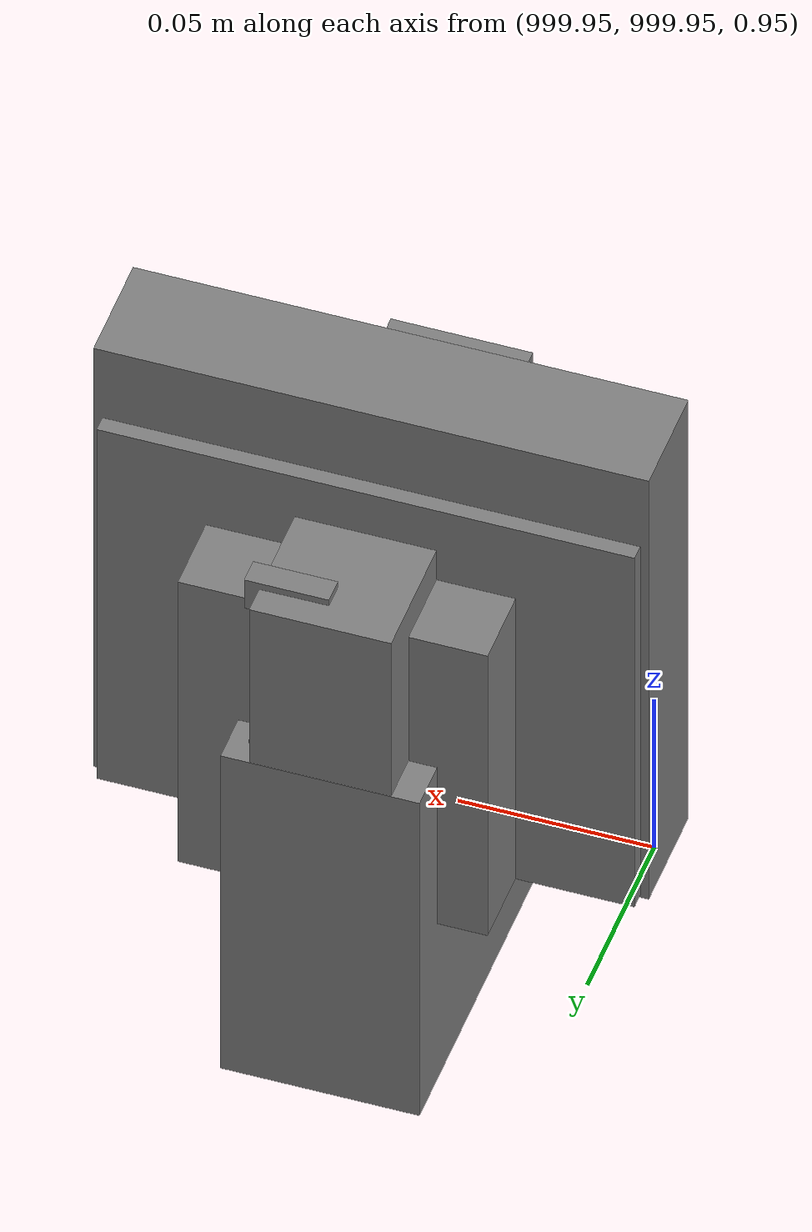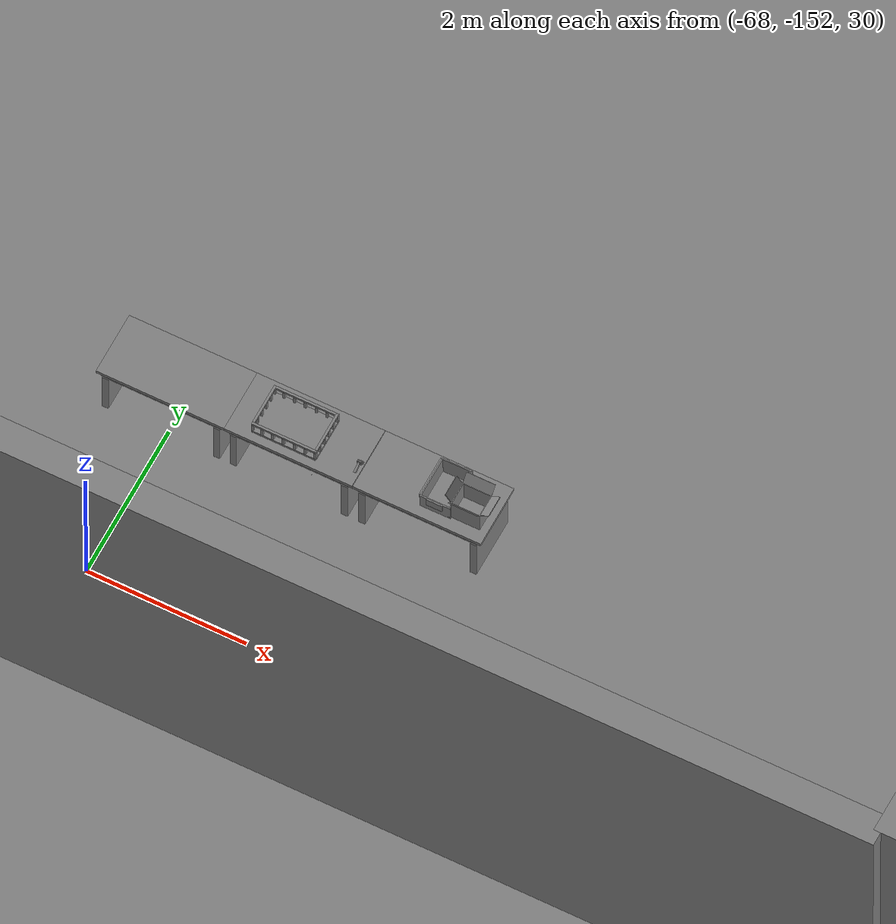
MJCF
<mujoco>
    <option gravity="0.000000000 0.000000000 -9.810000420" timestep="0.0049999999" integrator="implicitfast" density="1.225" viscosity="1.8000001e-05" noslip_iterations="10" iterations="100" sdf_iterations="50">
        <flag multiccd="disable"/>
    </option>
    <size memory="1000M"/>
    <compiler coordinate="local"/>
    <worldbody>
        <light cutoff="30" pos="0 1 1" dir="0 -1 -2"/>
        <light cutoff="30" pos="0 -1 1" dir="0 1 -2"/>
        <body pos="-64.866622925 -149.383972168 30.183746338" euler="89.999984741 89.999946594 0.000000000" name="openloong_gripper_2f85_fix_base_usda_bluebox_01">
            <geom contype="1" conaffinity="1" density="1000" type="box" material="" rgba="0.500000000 0.500000000 0.500000000 1.000000000" solimp="0.899999976 0.949999988 0.001000000" friction="1.000000000 0.005000000 0.000100000" solref="0.020000000 1.000000000" margin="0" condim="3" group="0" pos="0.276580811 0.187225342 0.000068665" quat="0.707106948 0.000077471 0.707106352 0.000077486" size="0.100000001 0.057999998 0.010000000" name="openloong_gripper_2f85_fix_base_usda_geom_5E4163BF_F9D8_463F_8250_88E02C7BA43A"/>
            <geom contype="1" conaffinity="1" density="1000" type="box" material="" rgba="0.500000000 0.500000000 0.500000000 1.000000000" solimp="0.899999976 0.949999988 0.001000000" friction="1.000000000 0.005000000 0.000100000" solref="0.020000000 1.000000000" margin="0" condim="3" group="0" pos="0.000000000 0.002883911 0.000000000" quat="0.999999881 0.000000000 0.000000000 0.000000000" size="0.254000008 0.003000000 0.172000006" name="openloong_gripper_2f85_fix_base_usda_geom_11E46953_D577_43A0_9012_614F647EB0A9"/>
            <geom contype="1" conaffinity="1" density="1000" type="box" material="" rgba="0.500000000 0.500000000 0.500000000 1.000000000" solimp="0.899999976 0.949999988 0.001000000" friction="1.000000000 0.005000000 0.000100000" solref="0.020000000 1.000000000" margin="0" condim="3" group="0" pos="0.000000000 0.124874115 0.173484802" quat="0.999796331 0.020176515 -0.000000015 0.000000030" size="0.259999990 0.119999997 0.007000000" name="openloong_gripper_2f85_fix_base_usda_geom_80D8DF7B_C545_4B65_BCBC_3DFBDA7BAF49"/>
            <geom contype="1" conaffinity="1" density="1000" type="box" material="" rgba="0.500000000 0.500000000 0.500000000 1.000000000" solimp="0.899999976 0.949999988 0.001000000" friction="1.000000000 0.005000000 0.000100000" solref="0.020000000 1.000000000" margin="0" condim="3" group="0" pos="0.000000000 0.124874115 -0.173469543" quat="0.999796331 -0.020176545 -0.000000015 0.000000000" size="0.259999990 0.119999997 0.007000000" name="openloong_gripper_2f85_fix_base_usda_geom_8AB86845_A64F_44B8_8A3A_19F5EF3CABB1"/>
            <geom contype="1" conaffinity="1" density="1000" type="box" material="" rgba="0.500000000 0.500000000 0.500000000 1.000000000" solimp="0.899999976 0.949999988 0.001000000" friction="1.000000000 0.005000000 0.000100000" solref="0.020000000 1.000000000" margin="0" condim="3" group="0" pos="0.000000000 0.214008331 0.188980103" quat="0.999912977 0.013176724 0.000000015 0.000000000" size="0.259999990 0.029999999 0.012500000" name="openloong_gripper_2f85_fix_base_usda_geom_093E51DC_8B14_4C26_8340_6C025CA69F2C"/>
            <geom contype="1" conaffinity="1" density="1000" type="box" material="" rgba="0.500000000 0.500000000 0.500000000 1.000000000" solimp="0.899999976 0.949999988 0.001000000" friction="1.000000000 0.005000000 0.000100000" solref="0.020000000 1.000000000" margin="0" condim="3" group="0" pos="-0.258361816 0.125289917 0.001876831" quat="0.702796936 -0.020792112 0.710783124 0.020769298" size="0.189999998 0.119999997 0.009000000" name="openloong_gripper_2f85_fix_base_usda_geom_D3293A29_8172_4AD2_A5B7_52BC7623598C"/>
            <geom contype="1" conaffinity="1" density="1000" type="box" material="" rgba="0.500000000 0.500000000 0.500000000 1.000000000" solimp="0.899999976 0.949999988 0.001000000" friction="1.000000000 0.005000000 0.000100000" solref="0.020000000 1.000000000" margin="0" condim="3" group="0" pos="0.000000000 0.214008331 -0.188980103" quat="0.999912977 -0.013176769 0.000000030 0.000000015" size="0.259999990 0.029999999 0.012500000" name="openloong_gripper_2f85_fix_base_usda_geom_80FB95F5_2CB4_445B_8279_56EDA89198B7"/>
            <geom contype="1" conaffinity="1" density="1000" type="box" material="" rgba="0.500000000 0.500000000 0.500000000 1.000000000" solimp="0.899999976 0.949999988 0.001000000" friction="1.000000000 0.005000000 0.000100000" solref="0.020000000 1.000000000" margin="0" condim="3" group="0" pos="-0.276611328 0.187225342 0.000068665" quat="0.707106650 0.000077441 0.707106709 0.000077456" size="0.100000001 0.057999998 0.010000000" name="openloong_gripper_2f85_fix_base_usda_geom_F2A84F5D_F581_44F2_BCDA_6DDD0C0EBCFB"/>
            <geom contype="1" conaffinity="1" density="1000" type="box" material="" rgba="0.500000000 0.500000000 0.500000000 1.000000000" solimp="0.899999976 0.949999988 0.001000000" friction="1.000000000 0.005000000 0.000100000" solref="0.020000000 1.000000000" margin="0" condim="3" group="0" pos="0.258331299 0.125289917 0.001876831" quat="0.702851415 0.018856421 0.710823774 -0.019329369" size="0.189999998 0.119999997 0.009000000" name="openloong_gripper_2f85_fix_base_usda_geom_B7091990_F6BC_4371_B895_12C3AA72DDE7"/>
            <freejoint name="openloong_gripper_2f85_fix_base_usda_bluebox_01_joint"/>
            <site size="0.005000000 0.005000000 0.005000000" rgba="0.500000000 0.500000000 0.500000000 1.000000000" pos="0.000000000 0.000000000 0.000000000" quat="0.999961913 0.008726534 0.000000000 0.000000000" group="0" type="sphere" name="openloong_gripper_2f85_fix_base_usda_bluebox_01site"/>
        </body>
        <body pos="-64.496299744 -149.491867065 30.235729218" euler="0.000000000 0.000000000 89.999946594" name="openloong_gripper_2f85_fix_base_usda_cardboardbox_01">
            <geom contype="1" conaffinity="1" density="1000" type="box" material="" rgba="0.500000000 0.500000000 0.500000000 1.000000000" solimp="0.899999976 0.949999988 0.001000000" friction="1.000000000 0.005000000 0.000100000" solref="0.020000000 1.000000000" margin="0" condim="3" group="0" pos="-0.003166199 -0.004086494 0.005052090" quat="1.000000000 0.000000000 0.000000000 0.000000000" size="0.142499998 0.177500010 0.005000000" name="openloong_gripper_2f85_fix_base_usda_geom_50AD4BE2_C008_4964_BD73_EA4473523FB7"/>
            <geom contype="1" conaffinity="1" density="1000" type="box" material="" rgba="0.500000000 0.500000000 0.500000000 1.000000000" solimp="0.899999976 0.949999988 0.001000000" friction="1.000000000 0.005000000 0.000100000" solref="0.020000000 1.000000000" margin="0" condim="3" group="0" pos="-0.003166199 0.170316696 0.150570869" quat="1.000000000 0.000000000 0.000000000 0.000000000" size="0.142499998 0.005000000 0.149999991" name="openloong_gripper_2f85_fix_base_usda_geom_31B5B18B_0653_468D_BC9F_CFE65D5668A5"/>
            <geom contype="1" conaffinity="1" density="1000" type="box" material="" rgba="0.500000000 0.500000000 0.500000000 1.000000000" solimp="0.899999976 0.949999988 0.001000000" friction="1.000000000 0.005000000 0.000100000" solref="0.020000000 1.000000000" margin="0" condim="3" group="0" pos="-0.147399902 -0.005307198 0.150570869" quat="1.000000000 0.000000000 0.000000000 0.000000000" size="0.005000000 0.177500010 0.149999991" name="openloong_gripper_2f85_fix_base_usda_geom_0B89028A_4720_4EC6_97A5_20EB149FB539"/>
            <geom contype="1" conaffinity="1" density="1000" type="box" material="" rgba="0.500000000 0.500000000 0.500000000 1.000000000" solimp="0.899999976 0.949999988 0.001000000" friction="1.000000000 0.005000000 0.000100000" solref="0.020000000 1.000000000" margin="0" condim="3" group="0" pos="0.140275955 -0.005307198 0.150570869" quat="1.000000000 0.000000000 0.000000000 0.000000000" size="0.005000000 0.177500010 0.149999991" name="openloong_gripper_2f85_fix_base_usda_geom_363F332F_17D4_4F35_A67A_DA63C588FB4D"/>
            <geom contype="1" conaffinity="1" density="1000" type="box" material="" rgba="0.500000000 0.500000000 0.500000000 1.000000000" solimp="0.899999976 0.949999988 0.001000000" friction="1.000000000 0.005000000 0.000100000" solref="0.020000000 1.000000000" margin="0" condim="3" group="0" pos="-0.003166199 -0.181550980 0.150570869" quat="1.000000000 0.000000000 0.000000000 0.000000000" size="0.142499998 0.005000000 0.149999991" name="openloong_gripper_2f85_fix_base_usda_geom_3DB82DA9_BA4E_4D5F_A050_04570560E08E"/>
            <freejoint name="openloong_gripper_2f85_fix_base_usda_cardboardbox_01_joint"/>
            <site size="0.005000000 0.005000000 0.005000000" rgba="0.500000000 0.500000000 0.500000000 1.000000000" pos="0.000000000 0.000000000 0.000000000" quat="0.999961913 0.008726535 0.000000000 0.000000000" group="0" type="sphere" name="openloong_gripper_2f85_fix_base_usda_site_01797989_3F0E_4840_BA76_C22AE85A0B13"/>
            <body pos="0.139160156 -0.004048347 0.301930904" euler="-179.999954224 49.383502960 179.999954224" name="openloong_gripper_2f85_fix_base_usda_A1_006">
                <geom contype="1" conaffinity="1" density="1000" type="box" material="" rgba="0.500000000 0.500000000 0.500000000 1.000000000" solimp="0.899999976 0.949999988 0.001000000" friction="1.000000000 0.005000000 0.000100000" solref="0.020000000 1.000000000" margin="0" condim="3" group="0" pos="-0.071587563 0.000009537 0.001745224" quat="0.999999881 0.000000000 0.000000000 0.000000000" size="0.071249999 0.179999992 0.002500000" name="openloong_gripper_2f85_fix_base_usda_geom_D94AB631_D730_4585_970D_68FF264B0E55"/>
                <joint armature="0" stiffness="0.07" damping="0.0099999998" axis="0.000000 1.000000 0.000000" type="hinge" name="openloong_gripper_2f85_fix_base_usda_A1_006"/>
            </body>
            <body pos="-0.145902634 -0.004086494 0.301938057" euler="-180.000000000 -60.000011444 -180.000000000" name="openloong_gripper_2f85_fix_base_usda_A2_006">
                <geom contype="1" conaffinity="1" density="1000" type="box" material="" rgba="0.500000000 0.500000000 0.500000000 1.000000000" solimp="0.899999976 0.949999988 0.001000000" friction="1.000000000 0.005000000 0.000100000" solref="0.020000000 1.000000000" margin="0" condim="3" group="0" pos="0.071268082 0.000009537 0.002717972" quat="0.000002921 0.000000000 -0.000000030 0.999999881" size="0.071249999 0.179999992 0.002500000" name="openloong_gripper_2f85_fix_base_usda_geom_72658C39_4C48_4B59_B167_79D923221647"/>
                <joint armature="0" stiffness="0.07" damping="0.0099999998" axis="0.000000 1.000000 0.000000" type="hinge" name="openloong_gripper_2f85_fix_base_usda_A2_006"/>
            </body>
            <body pos="-0.003385544 0.175991058 0.301930904" euler="-125.858116150 -0.000004561 0.000002331" name="openloong_gripper_2f85_fix_base_usda_B2_006">
                <geom contype="1" conaffinity="1" density="1000" type="box" material="" rgba="0.500000000 0.500000000 0.500000000 1.000000000" solimp="0.899999976 0.949999988 0.001000000" friction="1.000000000 0.005000000 0.000100000" solref="0.020000000 1.000000000" margin="0" condim="3" group="0" pos="0.000009537 -0.070939064 -0.002470016" quat="0.999614120 0.027776197 -0.000000015 0.000000030" size="0.137500003 0.064999998 0.005000000" name="openloong_gripper_2f85_fix_base_usda_geom_0C69C932_8E9D_4A88_AE24_49CE7D9DB3F4"/>
                <joint armature="0" stiffness="0.07" damping="0.0099999998" axis="1.000000 0.000000 0.000000" type="hinge" name="openloong_gripper_2f85_fix_base_usda_B2_006"/>
            </body>
            <body pos="-0.003385544 -0.184140205 0.301938057" euler="147.805557251 0.000000000 0.000000000" name="openloong_gripper_2f85_fix_base_usda_B1_006">
                <geom contype="1" conaffinity="1" density="1000" type="box" material="" rgba="0.500000000 0.500000000 0.500000000 1.000000000" solimp="0.899999976 0.949999988 0.001000000" friction="1.000000000 0.005000000 0.000100000" solref="0.020000000 1.000000000" margin="0" condim="3" group="0" pos="-0.000028610 0.070202351 -0.002703667" quat="0.999614179 -0.027776167 0.000000000 0.000000000" size="0.137500003 0.064999998 0.005000000" name="openloong_gripper_2f85_fix_base_usda_geom_477B4D16_174C_458A_ACF2_9C2F805EF51F"/>
                <joint armature="0" stiffness="0.07" damping="0.0099999998" axis="1.000000 0.000000 0.000000" type="hinge" name="openloong_gripper_2f85_fix_base_usda_B1_006"/>
            </body>
        </body>
        <body pos="-65.882858276 -149.481979370 30.229999542" euler="-64.487716675 0.000000000 0.000000000" name="openloong_gripper_2f85_fix_base_usda_Barcode">
            <geom contype="1" conaffinity="1" density="1000" type="box" material="" rgba="0.500000000 0.500000000 0.500000000 1.000000000" solimp="0.899999976 0.949999988 0.001000000" friction="1.000000000 0.005000000 0.000100000" solref="0.020000000 1.000000000" margin="0" condim="3" group="0" pos="0.000000000 0.013038635 0.001419067" quat="0.000000000 0.000000000 0.000000000 1.000000119" size="0.034000002 0.010000000 0.017999999" name="openloong_gripper_2f85_fix_base_usda_geom_83BB7F15_1524_412C_87BC_4229AC6624A7"/>
            <geom contype="1" conaffinity="1" density="1000" type="box" material="" rgba="0.500000000 0.500000000 0.500000000 1.000000000" solimp="0.899999976 0.949999988 0.001000000" friction="1.000000000 0.005000000 0.000100000" solref="0.020000000 1.000000000" margin="0" condim="3" group="0" pos="0.000000000 -0.035301208 -0.007095337" quat="0.000000000 0.000000000 -0.043619365 0.999048233" size="0.028999999 0.010000000 0.020000000" name="openloong_gripper_2f85_fix_base_usda_geom_BB4A4D20_4DA8_40BC_BE7B_FFBD80F9ED31"/>
            <geom contype="1" conaffinity="1" density="1000" type="box" material="" rgba="0.500000000 0.500000000 0.500000000 1.000000000" solimp="0.899999976 0.949999988 0.001000000" friction="1.000000000 0.005000000 0.000100000" solref="0.020000000 1.000000000" margin="0" condim="3" group="0" pos="0.000000000 -0.043411255 -0.011749268" quat="0.922262907 0.386563420 0.000000000 0.000000000" size="0.026000001 0.010000000 0.020000000" name="openloong_gripper_2f85_fix_base_usda_geom_9131DBDD_3D01_458B_A64D_EC9AE3611D34"/>
            <geom contype="1" conaffinity="1" density="1000" type="box" material="" rgba="0.500000000 0.500000000 0.500000000 1.000000000" solimp="0.899999976 0.949999988 0.001000000" friction="1.000000000 0.005000000 0.000100000" solref="0.020000000 1.000000000" margin="0" condim="3" group="0" pos="0.000000000 -0.016967773 -0.031860352" quat="0.000000000 0.000000000 0.000000000 1.000000119" size="0.008000000 0.010000000 0.013000000" name="openloong_gripper_2f85_fix_base_usda_geom_E049EF3C_3EB9_476B_ACFB_110F98368D31"/>
            <geom contype="1" conaffinity="1" density="1000" type="box" material="" rgba="0.500000000 0.500000000 0.500000000 1.000000000" solimp="0.899999976 0.949999988 0.001000000" friction="1.000000000 0.005000000 0.000100000" solref="0.020000000 1.000000000" margin="0" condim="3" group="0" pos="0.000000000 -0.001869202 0.000312805" quat="0.953716993 0.300705761 0.000000000 0.000000000" size="0.032000002 0.010000000 0.018999999" name="openloong_gripper_2f85_fix_base_usda_geom_D19C3032_437E_4F04_9538_0CEDE09D0875"/>
            <geom contype="1" conaffinity="1" density="1000" type="box" material="" rgba="0.500000000 0.500000000 0.500000000 1.000000000" solimp="0.899999976 0.949999988 0.001000000" friction="1.000000000 0.005000000 0.000100000" solref="0.020000000 1.000000000" margin="0" condim="3" group="0" pos="0.000000000 -0.019531250 -0.003173828" quat="0.953716993 0.300705761 0.000000000 0.000000000" size="0.030999999 0.010000000 0.020000000" name="openloong_gripper_2f85_fix_base_usda_geom_7994136C_C1CF_4A6C_9386_E01DB6298955"/>
            <geom contype="1" conaffinity="1" density="1000" type="box" material="" rgba="0.500000000 0.500000000 0.500000000 1.000000000" solimp="0.899999976 0.949999988 0.001000000" friction="1.000000000 0.005000000 0.000100000" solref="0.020000000 1.000000000" margin="0" condim="3" group="0" pos="0.000000000 -0.035301208 -0.007095337" quat="0.953716993 0.300705761 0.000000000 0.000000000" size="0.028999999 0.010000000 0.020000000" name="openloong_gripper_2f85_fix_base_usda_geom_A4AE57B9_53F4_4F2C_9815_0683F20606E9"/>
            <geom contype="1" conaffinity="1" density="1000" type="box" material="" rgba="0.500000000 0.500000000 0.500000000 1.000000000" solimp="0.899999976 0.949999988 0.001000000" friction="1.000000000 0.005000000 0.000100000" solref="0.020000000 1.000000000" margin="0" condim="3" group="0" pos="0.000000000 -0.042617798 -0.071121216" quat="0.000000000 0.000000000 0.000000000 1.000000119" size="0.013000000 0.021000000 0.059999999" name="openloong_gripper_2f85_fix_base_usda_geom_8B88DCBF_7671_45FA_940F_0939E50933FD"/>
            <freejoint name="openloong_gripper_2f85_fix_base_usda_Barcode_joint"/>
            <site size="0.005000000 0.005000000 0.005000000" rgba="0.500000000 0.500000000 0.500000000 1.000000000" pos="0.000000000 0.000000000 0.000000000" quat="1.000000000 0.000000000 0.000000000 0.000000000" group="0" type="sphere" name="openloong_gripper_2f85_fix_base_usda_Barcode_site"/>
        </body>
        <body pos="-66.745018005 -149.392349243 30.184000015" euler="0.000000000 0.000000000 89.999946594" name="[22333542633238]_Basket_01">
            <geom contype="1" conaffinity="1" density="1000" type="box" material="" rgba="0.500000000 0.500000000 0.500000000 1.000000000" solimp="0.899999976 0.949999988 0.001000000" friction="1.000000000 0.005000000 0.000100000" solref="0.020000000 1.000000000" margin="0" condim="3" group="0" pos="-0.052425385 0.389207840 0.089787483" quat="0.707107008 0.000000000 0.000000000 0.707106411" size="0.014249999 0.014249999 0.059999999" name="[22333542633238]_geom_7F6DDECE_4592_47B8_A655_7D6988307483"/>
            <geom contype="1" conaffinity="1" density="1000" type="box" material="" rgba="0.500000000 0.500000000 0.500000000 1.000000000" solimp="0.899999976 0.949999988 0.001000000" friction="1.000000000 0.005000000 0.000100000" solref="0.020000000 1.000000000" margin="0" condim="3" group="0" pos="0.264015198 -0.133043289 0.089787483" quat="0.707107008 0.000000000 0.000000000 0.707106411" size="0.014249999 0.014249999 0.059999999" name="[22333542633238]_geom_FF4331DE_90A5_4662_9F0C_B13B57C6DBE0"/>
            <geom contype="1" conaffinity="1" density="1000" type="box" material="" rgba="0.500000000 0.500000000 0.500000000 1.000000000" solimp="0.899999976 0.949999988 0.001000000" friction="1.000000000 0.005000000 0.000100000" solref="0.020000000 1.000000000" margin="0" condim="3" group="0" pos="-0.264015198 -0.265548706 0.089793205" quat="0.707107008 0.000000000 0.000000000 0.707106411" size="0.014249999 0.014249999 0.059999999" name="[22333542633238]_geom_D361BCA7_0599_4809_9CB5_07430EF0FFD3"/>
            <geom contype="1" conaffinity="1" density="1000" type="box" material="" rgba="0.500000000 0.500000000 0.500000000 1.000000000" solimp="0.899999976 0.949999988 0.001000000" friction="1.000000000 0.005000000 0.000100000" solref="0.020000000 1.000000000" margin="0" condim="3" group="0" pos="-0.160263062 -0.389322281 0.089793205" quat="0.707107008 0.000000000 0.000000000 0.707106411" size="0.014249999 0.014249999 0.059999999" name="[22333542633238]_geom_282104D5_7A63_46A0_A42C_B19B8670E05A"/>
            <geom contype="1" conaffinity="1" density="1000" type="box" material="" rgba="0.500000000 0.500000000 0.500000000 1.000000000" solimp="0.899999976 0.949999988 0.001000000" friction="1.000000000 0.005000000 0.000100000" solref="0.020000000 1.000000000" margin="0" condim="3" group="0" pos="0.162265778 -0.389322281 0.089787483" quat="0.707107008 0.000000000 0.000000000 0.707106411" size="0.014249999 0.014249999 0.059999999" name="[22333542633238]_geom_97F640ED_F727_4DE7_896B_4A0B064F15A4"/>
            <geom contype="1" conaffinity="1" density="1000" type="box" material="" rgba="0.500000000 0.500000000 0.500000000 1.000000000" solimp="0.899999976 0.949999988 0.001000000" friction="1.000000000 0.005000000 0.000100000" solref="0.020000000 1.000000000" margin="0" condim="3" group="0" pos="0.264015198 0.389207840 0.089787483" quat="0.707107008 0.000000000 0.000000000 0.707106411" size="0.014249999 0.014249999 0.059999999" name="[22333542633238]_geom_0F40900B_4032_45B4_BD1A_3579AE6811C8"/>
            <geom contype="1" conaffinity="1" density="1000" type="box" material="" rgba="0.500000000 0.500000000 0.500000000 1.000000000" solimp="0.899999976 0.949999988 0.001000000" friction="1.000000000 0.005000000 0.000100000" solref="0.020000000 1.000000000" margin="0" condim="3" group="0" pos="-0.264015198 -0.133043289 0.089793205" quat="0.707107008 0.000000000 0.000000000 0.707106411" size="0.014249999 0.014249999 0.059999999" name="[22333542633238]_geom_65CDC781_D543_466C_979F_1464D7274EBB"/>
            <geom contype="1" conaffinity="1" density="1000" type="box" material="" rgba="0.500000000 0.500000000 0.500000000 1.000000000" solimp="0.899999976 0.949999988 0.001000000" friction="1.000000000 0.005000000 0.000100000" solref="0.020000000 1.000000000" margin="0" condim="3" group="0" pos="-0.264026642 0.269256592 0.089793205" quat="0.707107008 0.000000000 0.000000000 0.707106411" size="0.014249999 0.014249999 0.059999999" name="[22333542633238]_geom_7C45B893_11D2_4520_A20C_89142144A170"/>
            <geom contype="1" conaffinity="1" density="1000" type="box" material="" rgba="0.500000000 0.500000000 0.500000000 1.000000000" solimp="0.899999976 0.949999988 0.001000000" friction="1.000000000 0.005000000 0.000100000" solref="0.020000000 1.000000000" margin="0" condim="3" group="0" pos="0.054462433 0.389207840 0.089787483" quat="0.707107008 0.000000000 0.000000000 0.707106411" size="0.014249999 0.014249999 0.059999999" name="[22333542633238]_geom_F4FD90B9_D778_467A_A79E_0BF1C91F6C1A"/>
            <geom contype="1" conaffinity="1" density="1000" type="box" material="" rgba="0.500000000 0.500000000 0.500000000 1.000000000" solimp="0.899999976 0.949999988 0.001000000" friction="1.000000000 0.005000000 0.000100000" solref="0.020000000 1.000000000" margin="0" condim="3" group="0" pos="0.054462433 -0.389322281 0.089787483" quat="0.707107008 0.000000000 0.000000000 0.707106411" size="0.014249999 0.014249999 0.059999999" name="[22333542633238]_geom_2CD92660_B47E_4F86_B3C1_1057A5F04E90"/>
            <geom contype="1" conaffinity="1" density="1000" type="box" material="" rgba="0.500000000 0.500000000 0.500000000 1.000000000" solimp="0.899999976 0.949999988 0.001000000" friction="1.000000000 0.005000000 0.000100000" solref="0.020000000 1.000000000" margin="0" condim="3" group="0" pos="0.264015198 0.269256592 0.089793205" quat="0.707107008 0.000000000 0.000000000 0.707106411" size="0.014249999 0.014249999 0.059999999" name="[22333542633238]_geom_3D7CE5AD_505E_41BA_85F0_4328B97DE498"/>
            <geom contype="1" conaffinity="1" density="1000" type="box" material="" rgba="0.500000000 0.500000000 0.500000000 1.000000000" solimp="0.899999976 0.949999988 0.001000000" friction="1.000000000 0.005000000 0.000100000" solref="0.020000000 1.000000000" margin="0" condim="3" group="0" pos="0.264015198 -0.389322281 0.089787483" quat="0.707107008 0.000000000 0.000000000 0.707106411" size="0.014249999 0.014249999 0.059999999" name="[22333542633238]_geom_764BE12B_BE97_4F42_B949_72E5CA4B9775"/>
            <geom contype="1" conaffinity="1" density="1000" type="box" material="" rgba="0.500000000 0.500000000 0.500000000 1.000000000" solimp="0.899999976 0.949999988 0.001000000" friction="1.000000000 0.005000000 0.000100000" solref="0.020000000 1.000000000" margin="0" condim="3" group="0" pos="0.000000000 0.000000000 0.015998840" quat="0.707107008 0.000000000 0.000000000 0.707106411" size="0.403499991 0.279000014 0.015750000" name="[22333542633238]_geom_8CF8237F_DCEE_44B6_B4D0_090EF625EEED"/>
            <geom contype="1" conaffinity="1" density="1000" type="box" material="" rgba="0.500000000 0.500000000 0.500000000 1.000000000" solimp="0.899999976 0.949999988 0.001000000" friction="1.000000000 0.005000000 0.000100000" solref="0.020000000 1.000000000" margin="0" condim="3" group="0" pos="0.000000000 -0.389476776 0.163619041" quat="0.707107008 0.000000000 0.000000000 0.707106411" size="0.015000000 0.277500004 0.015750000" name="[22333542633238]_geom_686AEE1F_2CE1_433C_972E_5C082CE41E10"/>
            <geom contype="1" conaffinity="1" density="1000" type="box" material="" rgba="0.500000000 0.500000000 0.500000000 1.000000000" solimp="0.899999976 0.949999988 0.001000000" friction="1.000000000 0.005000000 0.000100000" solref="0.020000000 1.000000000" margin="0" condim="3" group="0" pos="0.162265778 0.389207840 0.089787483" quat="0.707107008 0.000000000 0.000000000 0.707106411" size="0.014249999 0.014249999 0.059999999" name="[22333542633238]_geom_9C5EE695_EBBC_4D15_8A43_34E2EB8913CB"/>
            <geom contype="1" conaffinity="1" density="1000" type="box" material="" rgba="0.500000000 0.500000000 0.500000000 1.000000000" solimp="0.899999976 0.949999988 0.001000000" friction="1.000000000 0.005000000 0.000100000" solref="0.020000000 1.000000000" margin="0" condim="3" group="0" pos="0.000000000 0.389471054 0.163619041" quat="0.707107008 0.000000000 0.000000000 0.707106411" size="0.015000000 0.277500004 0.015750000" name="[22333542633238]_geom_7FF6D840_4127_4F57_BAAB_81FE0B470BC6"/>
            <geom contype="1" conaffinity="1" density="1000" type="box" material="" rgba="0.500000000 0.500000000 0.500000000 1.000000000" solimp="0.899999976 0.949999988 0.001000000" friction="1.000000000 0.005000000 0.000100000" solref="0.020000000 1.000000000" margin="0" condim="3" group="0" pos="-0.263511658 0.000000000 0.163619041" quat="0.707107008 0.000000000 0.000000000 0.707106411" size="0.403499991 0.015000000 0.015750000" name="[22333542633238]_geom_710D3944_ABBF_4810_873F_75868BDF1A3C"/>
            <geom contype="1" conaffinity="1" density="1000" type="box" material="" rgba="0.500000000 0.500000000 0.500000000 1.000000000" solimp="0.899999976 0.949999988 0.001000000" friction="1.000000000 0.005000000 0.000100000" solref="0.020000000 1.000000000" margin="0" condim="3" group="0" pos="-0.264015198 0.141334534 0.089793205" quat="0.707107008 0.000000000 0.000000000 0.707106411" size="0.014249999 0.014249999 0.059999999" name="[22333542633238]_geom_00F51264_1FB8_42F9_8244_A22FF1092E99"/>
            <geom contype="1" conaffinity="1" density="1000" type="box" material="" rgba="0.500000000 0.500000000 0.500000000 1.000000000" solimp="0.899999976 0.949999988 0.001000000" friction="1.000000000 0.005000000 0.000100000" solref="0.020000000 1.000000000" margin="0" condim="3" group="0" pos="0.264015198 -0.265548706 0.089787483" quat="0.707107008 0.000000000 0.000000000 0.707106411" size="0.014249999 0.014249999 0.059999999" name="[22333542633238]_geom_E1E64BB3_3E62_4097_B31C_43F5DEF52732"/>
            <geom contype="1" conaffinity="1" density="1000" type="box" material="" rgba="0.500000000 0.500000000 0.500000000 1.000000000" solimp="0.899999976 0.949999988 0.001000000" friction="1.000000000 0.005000000 0.000100000" solref="0.020000000 1.000000000" margin="0" condim="3" group="0" pos="-0.160263062 0.389207840 0.089787483" quat="0.707107008 0.000000000 0.000000000 0.707106411" size="0.014249999 0.014249999 0.059999999" name="[22333542633238]_geom_3199AC64_1EEC_4792_B8E1_E7A8542B0C41"/>
            <geom contype="1" conaffinity="1" density="1000" type="box" material="" rgba="0.500000000 0.500000000 0.500000000 1.000000000" solimp="0.899999976 0.949999988 0.001000000" friction="1.000000000 0.005000000 0.000100000" solref="0.020000000 1.000000000" margin="0" condim="3" group="0" pos="-0.052425385 -0.389322281 0.089787483" quat="0.707107008 0.000000000 0.000000000 0.707106411" size="0.014249999 0.014249999 0.059999999" name="[22333542633238]_geom_489CA5BD_E65C_4B9B_B2D3_9ED6946617D6"/>
            <geom contype="1" conaffinity="1" density="1000" type="box" material="" rgba="0.500000000 0.500000000 0.500000000 1.000000000" solimp="0.899999976 0.949999988 0.001000000" friction="1.000000000 0.005000000 0.000100000" solref="0.020000000 1.000000000" margin="0" condim="3" group="0" pos="-0.264026642 -0.389322281 0.089793205" quat="0.707107008 0.000000000 0.000000000 0.707106411" size="0.014249999 0.014249999 0.059999999" name="[22333542633238]_geom_C51C1A2A_54F9_4B1D_B8D4_92FE1BCD18AA"/>
            <geom contype="1" conaffinity="1" density="1000" type="box" material="" rgba="0.500000000 0.500000000 0.500000000 1.000000000" solimp="0.899999976 0.949999988 0.001000000" friction="1.000000000 0.005000000 0.000100000" solref="0.020000000 1.000000000" margin="0" condim="3" group="0" pos="0.264015198 0.141334534 0.089787483" quat="0.707107008 0.000000000 0.000000000 0.707106411" size="0.014249999 0.014249999 0.059999999" name="[22333542633238]_geom_E991C9A6_2B56_40B7_B349_3EC43280F5EF"/>
            <geom contype="1" conaffinity="1" density="1000" type="box" material="" rgba="0.500000000 0.500000000 0.500000000 1.000000000" solimp="0.899999976 0.949999988 0.001000000" friction="1.000000000 0.005000000 0.000100000" solref="0.020000000 1.000000000" margin="0" condim="3" group="0" pos="-0.264015198 0.389207840 0.089793205" quat="0.707107008 0.000000000 0.000000000 0.707106411" size="0.014249999 0.014249999 0.059999999" name="[22333542633238]_geom_E1E01903_9A48_4187_85E0_A3520697FBAA"/>
            <geom contype="1" conaffinity="1" density="1000" type="box" material="" rgba="0.500000000 0.500000000 0.500000000 1.000000000" solimp="0.899999976 0.949999988 0.001000000" friction="1.000000000 0.005000000 0.000100000" solref="0.020000000 1.000000000" margin="0" condim="3" group="0" pos="0.264015198 0.004480362 0.089787483" quat="0.707107008 0.000000000 0.000000000 0.707106411" size="0.014249999 0.014249999 0.059999999" name="[22333542633238]_geom_D2DC44F1_9F0C_4ECD_B32F_E10960018B32"/>
            <geom contype="1" conaffinity="1" density="1000" type="box" material="" rgba="0.500000000 0.500000000 0.500000000 1.000000000" solimp="0.899999976 0.949999988 0.001000000" friction="1.000000000 0.005000000 0.000100000" solref="0.020000000 1.000000000" margin="0" condim="3" group="0" pos="0.263694763 -0.000011444 0.163619041" quat="0.707107008 0.000000000 0.000000000 0.707106411" size="0.403499991 0.015000000 0.015750000" name="[22333542633238]_geom_5D110D74_AD5E_4FEA_AC85_A0300A2BB6A1"/>
            <geom contype="1" conaffinity="1" density="1000" type="box" material="" rgba="0.500000000 0.500000000 0.500000000 1.000000000" solimp="0.899999976 0.949999988 0.001000000" friction="1.000000000 0.005000000 0.000100000" solref="0.020000000 1.000000000" margin="0" condim="3" group="0" pos="-0.264015198 0.004480362 0.089793205" quat="0.707107008 0.000000000 0.000000000 0.707106411" size="0.014249999 0.014249999 0.059999999" name="[22333542633238]_geom_C888E91B_2C7F_48A4_9376_ECE0B7173515"/>
            <freejoint name="[22333542633238]_joint_F0DE9055_2559_4775_B543_52ED9F24FDFC"/>
        </body>
        <body pos="0.000000000 0.000000000 0.000000000" euler="0.000000000 0.000000000 0.000000000" name="Static Objects_Static Objects">
            <geom contype="1" conaffinity="1" density="1000" type="box" material="" rgba="0.500000000 0.500000000 0.500000000 1.000000000" solimp="0.899999976 0.949999988 0.001000000" friction="1.000000000 0.005000000 0.000100000" solref="0.020000000 1.000000000" margin="0" condim="3" group="0" pos="-67.544113159 -149.365814209 29.727830887" quat="0.500000417 0.499999970 0.499999553 0.499999970" size="0.381000012 0.319999993 0.041000001" name="Static Objects_geom_6CFE501D_F986_4D84_99A2_11DF11ADD7F9"/>
            <geom contype="1" conaffinity="1" density="1000" type="box" material="" rgba="0.500000000 0.500000000 0.500000000 1.000000000" solimp="0.899999976 0.949999988 0.001000000" friction="1.000000000 0.005000000 0.000100000" solref="0.020000000 1.000000000" margin="0" condim="3" group="0" pos="-68.239501953 -149.365814209 30.086868286" quat="0.500000417 0.499999970 0.499999553 0.499999970" size="0.370999992 0.039500002 0.745000005" name="Static Objects_geom_DA0FB53C_6572_4385_9982_A9078E378FDB"/>
            <geom contype="1" conaffinity="1" density="1000" type="box" material="" rgba="0.500000000 0.500000000 0.500000000 1.000000000" solimp="0.899999976 0.949999988 0.001000000" friction="1.000000000 0.005000000 0.000100000" solref="0.020000000 1.000000000" margin="0" condim="3" group="0" pos="-68.239501953 -149.365814209 30.147235870" quat="0.500000417 0.499999970 0.499999553 0.499999970" size="0.400000006 0.022000000 0.800000012" name="Static Objects_geom_30CF3436_83A2_44AF_A983_0A997B4827E5"/>
            <geom contype="1" conaffinity="1" density="1000" type="box" material="" rgba="0.500000000 0.500000000 0.500000000 1.000000000" solimp="0.899999976 0.949999988 0.001000000" friction="1.000000000 0.005000000 0.000100000" solref="0.020000000 1.000000000" margin="0" condim="3" group="0" pos="-68.934890747 -149.365814209 29.727830887" quat="0.500000417 0.499999970 0.499999553 0.499999970" size="0.381000012 0.319999993 0.041000001" name="Static Objects_geom_932B08B7_C6BC_4358_8470_ADCE059A9BB2"/>
            <geom contype="1" conaffinity="1" density="1000" type="box" material="" rgba="0.500000000 0.500000000 0.500000000 1.000000000" solimp="0.899999976 0.949999988 0.001000000" friction="1.000000000 0.005000000 0.000100000" solref="0.020000000 1.000000000" margin="0" condim="3" group="0" pos="-68.239501953 -149.365814209 29.561563492" quat="0.500000417 0.499999970 0.499999553 0.499999970" size="0.020000000 0.022000000 0.660000026" name="Static Objects_geom_4614AC0F_F043_434C_8559_E58E4CC39B87"/>
            <geom contype="1" conaffinity="1" density="1000" type="box" material="" rgba="0.500000000 0.500000000 0.500000000 1.000000000" solimp="0.899999976 0.949999988 0.001000000" friction="1.000000000 0.005000000 0.000100000" solref="0.020000000 1.000000000" margin="0" condim="3" group="0" pos="-65.945671082 -149.365814209 29.727830887" quat="0.500000417 0.499999970 0.499999553 0.499999970" size="0.381000012 0.319999993 0.041000001" name="Static Objects_geom_05E836E8_A4A5_4627_99C9_6485256229D5"/>
            <geom contype="1" conaffinity="1" density="1000" type="box" material="" rgba="0.500000000 0.500000000 0.500000000 1.000000000" solimp="0.899999976 0.949999988 0.001000000" friction="1.000000000 0.005000000 0.000100000" solref="0.020000000 1.000000000" margin="0" condim="3" group="0" pos="-66.641059875 -149.365814209 30.086868286" quat="0.500000417 0.499999970 0.499999553 0.499999970" size="0.370999992 0.039500002 0.745000005" name="Static Objects_geom_FB4C9354_26FF_4FFE_A808_57F3F278A091"/>
            <geom contype="1" conaffinity="1" density="1000" type="box" material="" rgba="0.500000000 0.500000000 0.500000000 1.000000000" solimp="0.899999976 0.949999988 0.001000000" friction="1.000000000 0.005000000 0.000100000" solref="0.020000000 1.000000000" margin="0" condim="3" group="0" pos="-66.641059875 -149.365814209 30.147235870" quat="0.500000417 0.499999970 0.499999553 0.499999970" size="0.400000006 0.022000000 0.800000012" name="Static Objects_geom_0622A560_0032_4336_91E0_BE2A203278CC"/>
            <geom contype="1" conaffinity="1" density="1000" type="box" material="" rgba="0.500000000 0.500000000 0.500000000 1.000000000" solimp="0.899999976 0.949999988 0.001000000" friction="1.000000000 0.005000000 0.000100000" solref="0.020000000 1.000000000" margin="0" condim="3" group="0" pos="-67.336448669 -149.365814209 29.727830887" quat="0.500000417 0.499999970 0.499999553 0.499999970" size="0.381000012 0.319999993 0.041000001" name="Static Objects_geom_2A10828B_BE08_4C59_A768_B129A05F90E4"/>
            <geom contype="1" conaffinity="1" density="1000" type="box" material="" rgba="0.500000000 0.500000000 0.500000000 1.000000000" solimp="0.899999976 0.949999988 0.001000000" friction="1.000000000 0.005000000 0.000100000" solref="0.020000000 1.000000000" margin="0" condim="3" group="0" pos="-66.641059875 -149.365814209 29.561563492" quat="0.500000417 0.499999970 0.499999553 0.499999970" size="0.020000000 0.022000000 0.660000026" name="Static Objects_geom_B9DACEAA_06BA_4907_9B31_8E595ABF7B76"/>
            <geom contype="1" conaffinity="1" density="1000" type="box" material="" rgba="0.500000000 0.500000000 0.500000000 1.000000000" solimp="0.899999976 0.949999988 0.001000000" friction="1.000000000 0.005000000 0.000100000" solref="0.020000000 1.000000000" margin="0" condim="3" group="0" pos="-64.338577271 -149.365814209 29.727830887" quat="0.500000417 0.499999970 0.499999553 0.499999970" size="0.381000012 0.319999993 0.041000001" name="Static Objects_geom_C8798577_97EE_484A_AACD_3C4AB16BA6DC"/>
            <geom contype="1" conaffinity="1" density="1000" type="box" material="" rgba="0.500000000 0.500000000 0.500000000 1.000000000" solimp="0.899999976 0.949999988 0.001000000" friction="1.000000000 0.005000000 0.000100000" solref="0.020000000 1.000000000" margin="0" condim="3" group="0" pos="-65.033966064 -149.365814209 30.086868286" quat="0.500000417 0.499999970 0.499999553 0.499999970" size="0.370999992 0.039500002 0.745000005" name="Static Objects_geom_75117B1A_B724_4C8B_97A2_ACA54FDF4C61"/>
            <geom contype="1" conaffinity="1" density="1000" type="box" material="" rgba="0.500000000 0.500000000 0.500000000 1.000000000" solimp="0.899999976 0.949999988 0.001000000" friction="1.000000000 0.005000000 0.000100000" solref="0.020000000 1.000000000" margin="0" condim="3" group="0" pos="-65.033966064 -149.365814209 30.147235870" quat="0.500000417 0.499999970 0.499999553 0.499999970" size="0.400000006 0.022000000 0.800000012" name="Static Objects_geom_EE02C084_1B8C_40C1_A223_3BB6653958F8"/>
            <geom contype="1" conaffinity="1" density="1000" type="box" material="" rgba="0.500000000 0.500000000 0.500000000 1.000000000" solimp="0.899999976 0.949999988 0.001000000" friction="1.000000000 0.005000000 0.000100000" solref="0.020000000 1.000000000" margin="0" condim="3" group="0" pos="-65.729354858 -149.365814209 29.727830887" quat="0.500000417 0.499999970 0.499999553 0.499999970" size="0.381000012 0.319999993 0.041000001" name="Static Objects_geom_25C4EE7B_9CD2_41F7_AD58_ADFE918DE6F6"/>
            <geom contype="1" conaffinity="1" density="1000" type="box" material="" rgba="0.500000000 0.500000000 0.500000000 1.000000000" solimp="0.899999976 0.949999988 0.001000000" friction="1.000000000 0.005000000 0.000100000" solref="0.020000000 1.000000000" margin="0" condim="3" group="0" pos="-65.033966064 -149.365814209 29.561563492" quat="0.500000417 0.499999970 0.499999553 0.499999970" size="0.020000000 0.022000000 0.660000026" name="Static Objects_geom_D3E5FD84_7A30_4223_AE5B_9B6290BC97F7"/>
            <geom contype="1" conaffinity="1" density="1000" type="box" material="" rgba="0.500000000 0.500000000 0.500000000 1.000000000" solimp="0.899999976 0.949999988 0.001000000" friction="1.000000000 0.005000000 0.000100000" solref="0.020000000 1.000000000" margin="0" condim="3" group="0" pos="-61.754566193 -137.853729248 33.906845093" quat="0.707107067 0.000000000 0.000000000 0.707106471" size="0.759999990 0.759999990 4.500000000" name="Static Objects_geom_657CB300_9584_4021_89E3_5C8D139F01E0"/>
            <geom contype="1" conaffinity="1" density="1000" type="box" material="" rgba="0.500000000 0.500000000 0.500000000 1.000000000" solimp="0.899999976 0.949999988 0.001000000" friction="1.000000000 0.005000000 0.000100000" solref="0.020000000 1.000000000" margin="0" condim="3" group="0" pos="-57.511135101 -144.927108765 31.707921982" quat="1.000000000 0.000000000 0.000000000 0.000000000" size="0.200000003 8.000000000 2.299999952" name="Static Objects_geom_2E926DFA_E0F2_4E51_B397_36F354A65FC9"/>
            <geom contype="1" conaffinity="1" density="1000" type="box" material="" rgba="0.500000000 0.500000000 0.500000000 1.000000000" solimp="0.899999976 0.949999988 0.001000000" friction="1.000000000 0.005000000 0.000100000" solref="0.020000000 1.000000000" margin="0" condim="3" group="0" pos="-80.517646790 -157.574050903 31.688196182" quat="0.707107067 0.000000000 0.000000000 0.707106471" size="0.600000024 0.600000024 2.299999952" name="Static Objects_geom_4D26C037_BDF5_475E_A39B_104DD32C6932"/>
            <geom contype="1" conaffinity="1" density="1000" type="box" material="" rgba="0.500000000 0.500000000 0.500000000 1.000000000" solimp="0.899999976 0.949999988 0.001000000" friction="1.000000000 0.005000000 0.000100000" solref="0.020000000 1.000000000" margin="0" condim="3" group="0" pos="-80.711044312 -147.414932251 31.666158676" quat="1.000000000 0.000000000 0.000000000 0.000000000" size="0.200000003 10.000000000 2.299999952" name="Static Objects_geom_4F56A003_38AE_4F38_A99E_4ECA3B0E009B"/>
            <geom contype="1" conaffinity="1" density="1000" type="box" material="" rgba="0.500000000 0.500000000 0.500000000 1.000000000" solimp="0.899999976 0.949999988 0.001000000" friction="1.000000000 0.005000000 0.000100000" solref="0.020000000 1.000000000" margin="0" condim="3" group="0" pos="-57.687217712 -137.434692383 31.688196182" quat="0.707107067 0.000000000 0.000000000 0.707106471" size="0.600000024 0.600000024 2.299999952" name="Static Objects_geom_B1208E43_1D7B_4803_8E86_4E8259568420"/>
            <geom contype="1" conaffinity="1" density="1000" type="box" material="" rgba="0.500000000 0.500000000 0.500000000 1.000000000" solimp="0.899999976 0.949999988 0.001000000" friction="1.000000000 0.005000000 0.000100000" solref="0.020000000 1.000000000" margin="0" condim="3" group="0" pos="-69.537033081 -140.263229370 31.714921951" quat="0.707107067 0.000000000 0.000000000 0.707106471" size="0.759999990 4.500000000 2.299999952" name="Static Objects_geom_9A912FA7_08F7_4D25_90FA_5D849571D3F6"/>
            <geom contype="1" conaffinity="1" density="1000" type="box" material="" rgba="0.500000000 0.500000000 0.500000000 1.000000000" solimp="0.899999976 0.949999988 0.001000000" friction="1.000000000 0.005000000 0.000100000" solref="0.020000000 1.000000000" margin="0" condim="3" group="0" pos="-80.073638916 -137.853713989 33.906845093" quat="0.707107067 0.000000000 0.000000000 0.707106471" size="0.759999990 0.759999990 4.500000000" name="Static Objects_geom_B4E03AF8_AB5A_463F_9D38_A4F590C731D3"/>
            <geom contype="1" conaffinity="1" density="1000" type="box" material="" rgba="0.500000000 0.500000000 0.500000000 1.000000000" solimp="0.899999976 0.949999988 0.001000000" friction="1.000000000 0.005000000 0.000100000" solref="0.020000000 1.000000000" margin="0" condim="3" group="0" pos="-73.406707764 -155.734664917 31.707921982" quat="1.000000000 0.000000000 0.000000000 0.000000000" size="0.200000003 3.000000000 2.299999952" name="Static Objects_geom_F6EAFA84_D85D_4BC3_9329_2749CB85E0B4"/>
            <geom contype="1" conaffinity="1" density="1000" type="box" material="" rgba="0.500000000 0.500000000 0.500000000 1.000000000" solimp="0.899999976 0.949999988 0.001000000" friction="1.000000000 0.005000000 0.000100000" solref="0.020000000 1.000000000" margin="0" condim="3" group="0" pos="-68.497543335 -137.448257446 31.707921982" quat="0.707107067 0.000000000 0.000000000 0.707106471" size="0.200000003 14.000000000 2.299999952" name="Static Objects_geom_2EEDEEAA_B030_431A_9F56_5CFCDB06AE69"/>
            <geom contype="1" conaffinity="1" density="1000" type="cylinder" material="" rgba="0.500000000 0.500000000 0.500000000 1.000000000" solimp="0.899999976 0.949999988 0.001000000" friction="1.000000000 0.005000000 0.000100000" solref="0.020000000 1.000000000" margin="0" condim="3" group="0" pos="-68.868522644 -142.134506226 31.711090088" quat="0.707107067 0.000000000 0.000000000 0.707106471" size="0.509999990 2.299999952 1.000000000" name="Static Objects_geom_97B17948_8B60_4332_A5B8_B00163850F82"/>
            <geom contype="1" conaffinity="1" density="1000" type="plane" material="" rgba="0.500000000 0.500000000 0.500000000 1.000000000" solimp="0.899999976 0.949999988 0.001000000" friction="1.000000000 0.005000000 0.000100000" solref="0.020000000 1.000000000" margin="0" condim="3" group="0" pos="-72.873703003 -147.131927490 29.409669876" quat="1.000000000 0.000000000 0.000000000 0.000000000" size="18.000000000 14.000000000 1.000000000" name="Static Objects_geom_D8155640_9AF1_4B3C_859E_B5B0DECE7C70"/>
            <geom contype="1" conaffinity="1" density="1000" type="box" material="" rgba="0.500000000 0.500000000 0.500000000 1.000000000" solimp="0.899999976 0.949999988 0.001000000" friction="1.000000000 0.005000000 0.000100000" solref="0.020000000 1.000000000" margin="0" condim="3" group="0" pos="-79.943580627 -157.782272339 31.707921982" quat="0.707107067 0.000000000 0.000000000 0.707106471" size="0.200000003 7.000000000 2.299999952" name="Static Objects_geom_BAA21BC5_CBE3_48B6_A025_EC61D1E4BA3D"/>
            <geom contype="1" conaffinity="1" density="1000" type="box" material="" rgba="0.500000000 0.500000000 0.500000000 1.000000000" solimp="0.899999976 0.949999988 0.001000000" friction="1.000000000 0.005000000 0.000100000" solref="0.020000000 1.000000000" margin="0" condim="3" group="0" pos="-65.421028137 -152.903442383 31.707921982" quat="0.707107067 0.000000000 0.000000000 0.707106471" size="0.200000003 7.800000191 2.299999952" name="Static Objects_geom_6673726C_0089_4153_91D4_51BC1EE9EF7F"/>
            <geom contype="1" conaffinity="1" density="1000" type="box" material="" rgba="0.500000000 0.500000000 0.500000000 1.000000000" solimp="0.899999976 0.949999988 0.001000000" friction="1.000000000 0.005000000 0.000100000" solref="0.020000000 1.000000000" margin="0" condim="3" group="0" pos="-74.776908875 -149.964416504 31.688196182" quat="1.000000000 0.000000000 0.000000000 0.000000000" size="0.600000024 0.409999996 2.299999952" name="Static Objects_geom_16FAEE77_164F_49DE_9AE3_853DCB412325"/>
            <geom contype="1" conaffinity="1" density="1000" type="cylinder" material="" rgba="0.500000000 0.500000000 0.500000000 1.000000000" solimp="0.899999976 0.949999988 0.001000000" friction="1.000000000 0.005000000 0.000100000" solref="0.020000000 1.000000000" margin="0" condim="3" group="0" pos="-60.161884308 -142.134506226 31.711090088" quat="0.707107067 0.000000000 0.000000000 0.707106471" size="0.509999990 2.299999952 1.000000000" name="Static Objects_geom_8CB03EA3_E475_4FE8_A242_92C41C28D6C0"/>
            <geom contype="1" conaffinity="1" density="1000" type="cylinder" material="" rgba="0.500000000 0.500000000 0.500000000 1.000000000" solimp="0.899999976 0.949999988 0.001000000" friction="1.000000000 0.005000000 0.000100000" solref="0.020000000 1.000000000" margin="0" condim="3" group="0" pos="-75.382453918 -149.963455200 31.711090088" quat="0.707107067 0.000000000 0.000000000 0.707106471" size="0.409999996 2.299999952 1.000000000" name="Static Objects_geom_BB173554_EF70_4750_A08E_7776B8F9B6D7"/>
            <geom contype="1" conaffinity="1" density="1000" type="cylinder" material="" rgba="0.500000000 0.500000000 0.500000000 1.000000000" solimp="0.899999976 0.949999988 0.001000000" friction="1.000000000 0.005000000 0.000100000" solref="0.020000000 1.000000000" margin="0" condim="3" group="0" pos="-74.154960632 -149.963455200 31.711090088" quat="0.707107067 0.000000000 0.000000000 0.707106471" size="0.409999996 2.299999952 1.000000000" name="Static Objects_geom_5654439C_AE05_44CB_B311_CA81A38F244D"/>
            <geom contype="1" conaffinity="1" density="1000" type="cylinder" material="" rgba="0.500000000 0.500000000 0.500000000 1.000000000" solimp="0.899999976 0.949999988 0.001000000" friction="1.000000000 0.005000000 0.000100000" solref="0.020000000 1.000000000" margin="0" condim="3" group="0" pos="-77.566612244 -142.134506226 31.711090088" quat="0.707107067 0.000000000 0.000000000 0.707106471" size="0.509999990 2.299999952 1.000000000" name="Static Objects_geom_FA6B97C9_55EA_4770_ABB8_380F6C93447C"/>
        </body>
        <body pos="1000.000000000 1000.000000000 1.000000000" euler="0.000011953 0.000005123 -179.999984741" name="openloong_gripper_2f85_fix_base_usda_intel_box">
            <geom contype="1" conaffinity="1" density="1000" type="box" material="" rgba="0.500000000 0.500000000 0.500000000 1.000000000" solimp="0.899999976 0.949999988 0.001000000" friction="1.000000000 0.005000000 0.000100000" solref="0.020000000 1.000000000" margin="0" condim="3" group="0" pos="0.000000000 -0.000067139 0.000082284" quat="0.707106709 0.000000225 0.000000253 0.707106650" size="0.052800003 0.025300000 0.052800003" name="openloong_gripper_2f85_fix_base_usda_geom_622847B0_A641_407E_AA8C_B3C53A7349A9"/>
            <freejoint name="openloong_gripper_2f85_fix_base_usda_intel_box_joint"/>
            <site size="0.005000000 0.005000000 0.005000000" rgba="0.500000000 0.500000000 0.500000000 1.000000000" pos="0.000000000 0.000000000 0.000000000" quat="0.999961913 0.008726500 0.000000000 0.000000000" group="0" type="sphere" name="openloong_gripper_2f85_fix_base_usda_intel_boxsite"/>
        </body>
        <body pos="1000.000000000 1000.000000000 1.000000000" euler="0.000000000 0.000000000 180.000000000" name="openloong_gripper_2f85_fix_base_usda_cpu_fan">
            <geom contype="1" conaffinity="1" density="1000" type="box" material="" rgba="0.500000000 0.500000000 0.500000000 1.000000000" solimp="0.899999976 0.949999988 0.001000000" friction="1.000000000 0.005000000 0.000100000" solref="0.020000000 1.000000000" margin="0" condim="3" group="0" pos="0.000000000 0.000000000 0.070034981" quat="0.000000000 0.000000000 0.000000000 1.000000000" size="0.070700005 0.014699999 0.070700005" name="openloong_gripper_2f85_fix_base_usda_geom_CC821C48_58DE_4923_A941_2AA3C3A697AC"/>
            <freejoint name="openloong_gripper_2f85_fix_base_usda_cpu_fan_joint"/>
            <site size="0.005000000 0.005000000 0.005000000" rgba="0.500000000 0.500000000 0.500000000 1.000000000" pos="0.000000000 0.000000000 0.000000000" quat="0.999961913 0.008726535 0.000000000 0.000000000" group="0" type="sphere" name="openloong_gripper_2f85_fix_base_usda_cpu_fancsite"/>
        </body>
        <body pos="1000.000000000 1000.000000000 1.000000000" euler="0.000000000 0.000000000 180.000000000" name="openloong_gripper_2f85_fix_base_usda_wifi_box">
            <geom contype="1" conaffinity="1" density="1000" type="box" material="" rgba="0.500000000 0.500000000 0.500000000 1.000000000" solimp="0.899999976 0.949999988 0.001000000" friction="1.000000000 0.005000000 0.000100000" solref="0.020000000 1.000000000" margin="0" condim="3" group="0" pos="0.000000000 0.000000000 0.058978677" quat="0.000000000 0.000000047 0.000000000 1.000000000" size="0.068499997 0.018999999 0.059000000" name="openloong_gripper_2f85_fix_base_usda_geom_452EE863_8C34_4D03_9F10_D0951D239B51"/>
            <freejoint name="openloong_gripper_2f85_fix_base_usda_wifi_box_joint"/>
            <site size="0.005000000 0.005000000 0.005000000" rgba="0.500000000 0.500000000 0.500000000 1.000000000" pos="0.000000000 0.000000000 0.000000000" quat="0.999961913 0.008726500 0.000000000 0.000000000" group="0" type="sphere" name="openloong_gripper_2f85_fix_base_usda_wifi_boxsite"/>
        </body>
        <body pos="1000.000000000 999.999938965 1.000000000" euler="0.000000000 0.000000000 180.000000000" name="openloong_gripper_2f85_fix_base_usda_intelcore_i5">
            <geom contype="1" conaffinity="1" density="1000" type="box" material="" rgba="0.500000000 0.500000000 0.500000000 1.000000000" solimp="0.899999976 0.949999988 0.001000000" friction="1.000000000 0.005000000 0.000100000" solref="0.020000000 1.000000000" margin="0" condim="3" group="0" pos="0.000000000 0.000000000 0.051722717" quat="0.707106709 0.000000000 0.000000000 -0.707106769" size="0.052800000 0.018080002 0.052800000" name="openloong_gripper_2f85_fix_base_usda_geom_3370EDA1_CCFB_4F89_8B19_538686B3AB92"/>
            <freejoint name="openloong_gripper_2f85_fix_base_usda_intelcore_i5_joint"/>
            <site size="0.005000000 0.005000000 0.005000000" rgba="0.500000000 0.500000000 0.500000000 1.000000000" pos="0.000000000 0.000000000 0.000000000" quat="0.999961913 0.008726534 0.000000000 0.000000000" group="0" type="sphere" name="openloong_gripper_2f85_fix_base_usda_intelcore_i5site"/>
        </body>
        <body pos="-66.070465088 -149.323287964 31.162883759" euler="99.504280090 18.031888962 147.080612183" mocap="true" name="spotlight1_SpotLight"/>
        <body pos="-66.393089294 -149.452957153 31.165716171" euler="42.530765533 -16.605802536 172.737701416" mocap="true" name="spotlight3_SpotLight"/>
        <body pos="1000.000000000 1000.000000000 1.000000000" euler="0.000000000 0.000000000 180.000000000" name="openloong_gripper_2f85_fix_base_usda_battery_01">
            <geom contype="1" conaffinity="1" density="1000" type="box" material="" rgba="0.500000000 0.500000000 0.500000000 1.000000000" solimp="0.899999976 0.949999988 0.001000000" friction="1.000000000 0.005000000 0.000100000" solref="0.020000000 1.000000000" margin="0" condim="3" group="0" pos="-0.011123657 -0.041940309 0.101691343" quat="1.000000000 0.000000000 0.000000000 0.000000000" size="0.010800000 0.003375000 0.004725000" name="openloong_gripper_2f85_fix_base_usda_geom_357D559C_9FBA_4BAA_936A_C6CEAD116121"/>
            <geom contype="1" conaffinity="1" density="1000" type="box" material="" rgba="0.500000000 0.500000000 0.500000000 1.000000000" solimp="0.899999976 0.949999988 0.001000000" friction="1.000000000 0.005000000 0.000100000" solref="0.020000000 1.000000000" margin="0" condim="3" group="0" pos="-0.010876465 -0.044247437 0.047066893" quat="0.998702705 -0.050920475 0.000000000 0.000000000" size="0.009450001 0.002700000 0.024975000" name="openloong_gripper_2f85_fix_base_usda_geom_6BC66B2E_F1A4_490A_9F9F_4B47EEDAFCA1"/>
            <geom contype="1" conaffinity="1" density="1000" type="box" material="" rgba="0.500000000 0.500000000 0.500000000 1.000000000" solimp="0.899999976 0.949999988 0.001000000" friction="1.000000000 0.005000000 0.000100000" solref="0.020000000 1.000000000" margin="0" condim="3" group="0" pos="-0.001235962 -0.000659180 0.047381196" quat="1.000000000 0.000000000 0.000000000 0.000000000" size="0.039420001 0.039150000 0.047250003" name="openloong_gripper_2f85_fix_base_usda_geom_045547DE_F8A0_4460_B525_890B4F9B4E3C"/>
            <geom contype="1" conaffinity="1" density="1000" type="box" material="" rgba="0.500000000 0.500000000 0.500000000 1.000000000" solimp="0.899999976 0.949999988 0.001000000" friction="1.000000000 0.005000000 0.000100000" solref="0.020000000 1.000000000" margin="0" condim="3" group="0" pos="-0.010876465 -0.039138794 0.009851727" quat="1.000000000 0.000000000 0.000000000 0.000000000" size="0.009450001 0.010800000 0.013500000" name="openloong_gripper_2f85_fix_base_usda_geom_203A32A3_72AC_4137_B480_75F09A9807B3"/>
            <geom contype="1" conaffinity="1" density="1000" type="box" material="" rgba="0.500000000 0.500000000 0.500000000 1.000000000" solimp="0.899999976 0.949999988 0.001000000" friction="1.000000000 0.005000000 0.000100000" solref="0.020000000 1.000000000" margin="0" condim="3" group="0" pos="-0.010876465 -0.041528322 0.071508206" quat="1.000000000 0.000000000 0.000000000 0.000000000" size="0.009450001 0.002700000 0.027000001" name="openloong_gripper_2f85_fix_base_usda_geom_C83267FB_D870_4AA7_BF94_4DFAF0C440C6"/>
            <freejoint name="openloong_gripper_2f85_fix_base_usda_battery_01_joint"/>
            <site size="0.005000000 0.005000000 0.005000000" rgba="0.500000000 0.500000000 0.500000000 1.000000000" pos="0.000000000 0.000000000 0.000000000" quat="0.999961913 0.008726500 0.000000000 0.000000000" group="0" type="sphere" name="openloong_gripper_2f85_fix_base_usda_battery_01site"/>
        </body>
        <body pos="-66.248214722 -149.251846313 31.168361664" euler="102.270378113 27.195617676 11.884142876" mocap="true" name="spotlight4_SpotLight"/>
        <body pos="-66.291030884 -149.869689941 29.018842697" euler="0.000000000 0.000000000 89.999946594" mocap="true" name="openloong_gripper_2f85_fix_base_usda_leftHandMocap"/>
        <body pos="-66.291030884 -149.869689941 29.018842697" euler="0.000000000 0.000000000 89.999946594" mocap="true" name="openloong_gripper_2f85_fix_base_usda_rightHandMocap"/>
        <body pos="-66.291030884 -149.869689941 30.218843460" euler="0.000000000 0.000000000 89.999946594" name="openloong_gripper_2f85_fix_base_usda_base_link">
            <geom contype="1" conaffinity="1" density="1000" type="mesh" material="" rgba="0.783999979 0.783999979 0.783999979 1.000000000" solimp="0.899999976 0.949999988 0.001000000" friction="1.000000000 0.005000000 0.000100000" solref="0.020000000 1.000000000" margin="0" condim="3" group="3" mesh="base_link" pos="0.000000000 0.000000000 0.000000000" quat="1.000000000 0.000000000 0.000000000 0.000000000" size="1.000000000 1.000000000 1.000000000" name="openloong_gripper_2f85_fix_base_usda__geom_7_7A5F0770_D0A4_4E79_B087_C62719A5D1F5"/>
            <site size="0.005000000 0.005000000 0.005000000" rgba="0.500000000 0.500000000 0.500000000 1.000000000" pos="0.000000000 0.000000000 0.000000000" quat="1.000000000 0.000000000 0.000000000 0.000000000" group="0" type="sphere" name="openloong_gripper_2f85_fix_base_usda_imu"/>
            <inertial mass="22.447001" pos="-0.005664100 -0.001336700 0.238289997" diaginertia="0.374352545 0.277180195 0.220617250" quat="0.999247074 0.035235517 -0.015086859 0.006023135"/>
            <body pos="0.000000000 0.000000000 0.299997330" euler="0.000000000 0.000000000 0.000000000" name="openloong_gripper_2f85_fix_base_usda_dummy_body">
                <geom contype="1" conaffinity="1" density="1000" type="sphere" material="" rgba="0.783999979 0.783999979 0.783999979 1.000000000" solimp="0.899999976 0.949999988 0.001000000" friction="1.000000000 0.005000000 0.000100000" solref="0.020000000 1.000000000" margin="0" condim="3" group="3" pos="0.000000000 0.000000000 0.000000000" quat="1.000000000 0.000000000 0.000000000 0.000000000" size="0.010000000 0.000000000 0.000000000" name="openloong_gripper_2f85_fix_base_usda__geom_8_23B1EFA8_B886_4A47_BBE9_6E1F087A8CD3"/>
                <joint armature="0.0099999998" stiffness="0" damping="0.1" axis="0.000000 0.000000 1.000000" type="hinge" name="openloong_gripper_2f85_fix_base_usda_dummy_joint"/>
                <site size="0.010000000 0.005000000 0.005000000" rgba="0.500000000 0.500000000 0.500000000 1.000000000" pos="0.000000000 0.000000000 0.000000000" quat="1.000000000 0.000000000 0.000000000 0.000000000" group="3" type="sphere" name="openloong_gripper_2f85_fix_base_usda_dummy_site"/>
            </body>
            <body pos="0.009002686 0.000000000 0.406400681" euler="0.000000000 0.000000000 0.000000000" name="openloong_gripper_2f85_fix_base_usda_Link_head_yaw">
                <geom contype="1" conaffinity="1" density="1000" type="mesh" material="" rgba="0.783999979 0.783999979 0.783999979 1.000000000" solimp="0.899999976 0.949999988 0.001000000" friction="1.000000000 0.005000000 0.000100000" solref="0.020000000 1.000000000" margin="0" condim="3" group="3" mesh="Link_head_yaw" pos="0.000000000 0.000000000 0.000000000" quat="1.000000000 0.000000000 0.000000000 0.000000000" size="1.000000000 1.000000000 1.000000000" name="openloong_gripper_2f85_fix_base_usda__geom_10_E05CFE81_D929_4798_A18F_E64010324516"/>
                <inertial mass="0.84249002" pos="0.000000000 -0.002081400 0.044801001" diaginertia="0.000700588 0.000629000 0.000553812" quat="0.706933022 -0.015675601 0.015677100 0.706933022"/>
                <body pos="0.000000000 -0.034599304 0.048500061" euler="0.000000000 0.000000000 0.000000000" name="openloong_gripper_2f85_fix_base_usda_Link_head_pitch">
                    <geom contype="1" conaffinity="1" density="1000" type="mesh" material="" rgba="0.783999979 0.783999979 0.783999979 1.000000000" solimp="0.899999976 0.949999988 0.001000000" friction="1.000000000 0.005000000 0.000100000" solref="0.020000000 1.000000000" margin="0" condim="3" group="3" mesh="Link_head_pitch" pos="0.000000000 0.000000000 0.000000000" quat="1.000000000 0.000000000 0.000000000 0.000000000" size="1.000000000 1.000000000 1.000000000" name="openloong_gripper_2f85_fix_base_usda__geom_12_F496E451_F4C6_4E61_A655_23483B1FC849"/>
                    <inertial mass="1.3943" pos="0.020569000 0.033004001 0.125000000" diaginertia="0.006381400 0.006289940 0.004481460" quat="0.973390222 0.008406822 0.228157058 0.019624906"/>
                    <body pos="0.000000000 0.029998779 0.000000000" euler="0.000000000 0.000000000 0.000000000" name="openloong_gripper_2f85_fix_base_usda_neck_center_body">
                        <site size="0.010000000 0.005000000 0.005000000" rgba="0.500000000 0.500000000 0.500000000 1.000000000" pos="0.000000000 0.000000000 0.000000000" quat="1.000000000 0.000000000 0.000000000 0.000000000" group="3" type="sphere" name="openloong_gripper_2f85_fix_base_usda_neck_center_site"/>
                        <body pos="0.020004272 0.000000000 0.149999619" euler="-0.000002229 39.998176575 -90.000205994" name="openloong_gripper_2f85_fix_base_usda_camera_head">
                            <site size="0.010000000 0.005000000 0.005000000" rgba="0.500000000 0.500000000 0.500000000 1.000000000" pos="0.000000000 0.000000000 0.000000000" quat="1.000000000 0.000000000 0.000000000 0.000000000" group="3" type="sphere" name="openloong_gripper_2f85_fix_base_usda_camera_head_site"/>
                        </body>
                    </body>
                </body>
            </body>
            <body pos="0.003997803 -0.161598206 0.392200470" euler="0.000000000 0.000000000 0.000000000" name="openloong_gripper_2f85_fix_base_usda_Link_arm_r_01">
                <geom contype="1" conaffinity="1" density="1000" type="mesh" material="" rgba="0.783999979 0.783999979 0.783999979 1.000000000" solimp="0.899999976 0.949999988 0.001000000" friction="1.000000000 0.005000000 0.000100000" solref="0.020000000 1.000000000" margin="0" condim="3" group="3" mesh="Link_arm_r_01" pos="0.000000000 0.000000000 0.000000000" quat="1.000000000 0.000000000 0.000000000 0.000000000" size="1.000000000 1.000000000 1.000000000" name="openloong_gripper_2f85_fix_base_usda__geom_14_B379E207_E8AF_493E_B544_DBC9C7B6D377"/>
                <joint armature="0.0099999998" stiffness="0" damping="1" axis="0.000000 -1.000000 0.000000" limited="true" range="-170.000015259 170.000015259" type="hinge" name="openloong_gripper_2f85_fix_base_usda_J_arm_r_01"/>
                <inertial mass="0.75641" pos="0.004494600 -0.038293999 -0.000001874" diaginertia="0.000842990 0.000803050 0.000587120" quat="-0.000163502 0.707098067 0.000812463 0.707115054"/>
                <body pos="-0.041992188 -0.041000366 0.000000000" euler="0.000000000 0.000000000 0.000000000" name="openloong_gripper_2f85_fix_base_usda_Link_arm_r_02">
                    <geom contype="1" conaffinity="1" density="1000" type="mesh" material="" rgba="0.783999979 0.783999979 0.783999979 1.000000000" solimp="0.899999976 0.949999988 0.001000000" friction="1.000000000 0.005000000 0.000100000" solref="0.020000000 1.000000000" margin="0" condim="3" group="3" mesh="Link_arm_r_02" pos="0.000000000 0.000000000 0.000000000" quat="1.000000000 0.000000000 0.000000000 0.000000000" size="1.000000000 1.000000000 1.000000000" name="openloong_gripper_2f85_fix_base_usda__geom_16_307C66F0_AD28_466E_9799_D47FDAF87AE4"/>
                    <joint armature="0.0099999998" stiffness="0" damping="1" axis="-1.000000 0.000000 0.000000" limited="true" range="-105.000244141 105.000244141" type="hinge" name="openloong_gripper_2f85_fix_base_usda_J_arm_r_02"/>
                    <inertial mass="0.98500001" pos="0.041999999 -0.067430697 0.000000000" diaginertia="0.002262690 0.001730990 0.001154020" quat="0.500000000 0.500000000 -0.500000000 0.500000000"/>
                    <body pos="0.041992188 -0.122596741 0.000000000" euler="0.000000000 0.000000000 0.000000000" name="openloong_gripper_2f85_fix_base_usda_Link_arm_r_03">
                        <geom contype="1" conaffinity="1" density="1000" type="mesh" material="" rgba="0.783999979 0.783999979 0.783999979 1.000000000" solimp="0.899999976 0.949999988 0.001000000" friction="1.000000000 0.005000000 0.000100000" solref="0.020000000 1.000000000" margin="0" condim="3" group="3" mesh="Link_arm_r_03" pos="0.000000000 0.000000000 0.000000000" quat="1.000000000 0.000000000 0.000000000 0.000000000" size="1.000000000 1.000000000 1.000000000" name="openloong_gripper_2f85_fix_base_usda__geom_18_33C56F43_3DE7_4DD0_A53C_06A5A3F21DB8"/>
                        <joint armature="0.0099999998" stiffness="0" damping="1" axis="0.000000 -1.000000 0.000000" limited="true" range="-170.000015259 170.000015259" type="hinge" name="openloong_gripper_2f85_fix_base_usda_J_arm_r_03"/>
                        <inertial mass="0.95899999" pos="-0.001413580 -0.164663002 0.020757901" diaginertia="0.002101340 0.002064590 0.000754802" quat="0.560480952 0.454391927 -0.443732947 0.531497955"/>
                        <body pos="0.035293579 -0.177406311 0.023998260" euler="0.000000000 0.000000000 0.000000000" name="openloong_gripper_2f85_fix_base_usda_Link_arm_r_04">
                            <geom contype="1" conaffinity="1" density="1000" type="mesh" material="" rgba="0.783999979 0.783999979 0.783999979 1.000000000" solimp="0.899999976 0.949999988 0.001000000" friction="1.000000000 0.005000000 0.000100000" solref="0.020000000 1.000000000" margin="0" condim="3" group="3" mesh="Link_arm_r_04" pos="0.000000000 0.000000000 0.000000000" quat="1.000000000 0.000000000 0.000000000 0.000000000" size="1.000000000 1.000000000 1.000000000" name="openloong_gripper_2f85_fix_base_usda__geom_20_7ABD1C83_1C25_4BC1_B58B_FEE3FFC3721E"/>
                            <joint armature="0.0099999998" stiffness="0" damping="1" axis="-1.000000 0.000000 0.000000" limited="true" range="0.000000000 170.000015259" type="hinge" name="openloong_gripper_2f85_fix_base_usda_J_arm_r_04"/>
                            <inertial mass="0.60000002" pos="-0.038727000 -0.060766999 -0.021003000" diaginertia="0.001092610 0.000712422 0.000645102" quat="0.327701002 0.632602990 -0.467366993 0.523443997"/>
                            <body pos="-0.035293579 -0.103492737 -0.023998260" euler="0.000000000 0.000000000 0.000000000" name="openloong_gripper_2f85_fix_base_usda_Link_arm_r_05">
                                <geom contype="1" conaffinity="1" density="1000" type="mesh" material="" rgba="0.783999979 0.783999979 0.783999979 1.000000000" solimp="0.899999976 0.949999988 0.001000000" friction="1.000000000 0.005000000 0.000100000" solref="0.020000000 1.000000000" margin="0" condim="3" group="3" mesh="Link_arm_r_05" pos="0.000000000 0.000000000 0.000000000" quat="1.000000000 0.000000000 0.000000000 0.000000000" size="1.000000000 1.000000000 1.000000000" name="openloong_gripper_2f85_fix_base_usda__geom_22_8D6FA18F_7AAA_41F7_AE1E_4D96AE11DD80"/>
                                <joint armature="0.0099999998" stiffness="0" damping="1" axis="0.000000 -1.000000 0.000000" limited="true" range="-170.000015259 170.000015259" type="hinge" name="openloong_gripper_2f85_fix_base_usda_J_arm_r_05"/>
                                <inertial mass="0.68976003" pos="0.000032712 -0.068658002 -0.000111780" diaginertia="0.002522510 0.002411100 0.000448695" quat="0.707660973 0.706543028 -0.002603360 0.002470550"/>
                                <body pos="-0.026489258 -0.196502686 0.000000000" euler="0.000000000 0.000000000 0.000000000" name="openloong_gripper_2f85_fix_base_usda_Link_arm_r_06">
                                    <geom contype="1" conaffinity="1" density="1000" type="mesh" material="" rgba="0.783999979 0.783999979 0.783999979 1.000000000" solimp="0.899999976 0.949999988 0.001000000" friction="1.000000000 0.005000000 0.000100000" solref="0.020000000 1.000000000" margin="0" condim="3" group="3" mesh="Link_arm_r_06" pos="0.000000000 0.000000000 0.000000000" quat="1.000000000 0.000000000 0.000000000 0.000000000" size="1.000000000 1.000000000 1.000000000" name="openloong_gripper_2f85_fix_base_usda__geom_24_005782FE_1354_4B6B_96A6_91392817F650"/>
                                    <joint armature="0.0099999998" stiffness="0" damping="1" axis="1.000000 0.000000 0.000000" limited="true" range="-105.000244141 105.000244141" type="hinge" name="openloong_gripper_2f85_fix_base_usda_J_arm_r_06"/>
                                    <inertial mass="0.28" pos="0.026078001 -0.000000896 0.001663700" diaginertia="0.000156930 0.000145601 0.000104979" quat="0.707080841 0.001851080 0.001883810 0.707127810"/>
                                    <body pos="0.026489258 0.000000000 0.031799316" euler="0.000000000 0.000000000 0.000000000" name="openloong_gripper_2f85_fix_base_usda_Link_arm_r_07">
                                        <geom contype="1" conaffinity="1" density="1000" type="mesh" material="" rgba="0.783999979 0.783999979 0.783999979 1.000000000" solimp="0.899999976 0.949999988 0.001000000" friction="1.000000000 0.005000000 0.000100000" solref="0.020000000 1.000000000" margin="0" condim="3" group="3" mesh="Link_arm_r_07" pos="0.000000000 0.000000000 0.000000000" quat="1.000000000 0.000000000 0.000000000 0.000000000" size="1.000000000 1.000000000 1.000000000" name="openloong_gripper_2f85_fix_base_usda__geom_26_799ED54B_C59C_4A92_83FA_F1009D84EF8E"/>
                                        <joint armature="0.0099999998" stiffness="0" damping="1" axis="0.000000 0.000000 1.000000" limited="true" range="-60.000133514 60.000133514" type="hinge" name="openloong_gripper_2f85_fix_base_usda_J_arm_r_07"/>
                                        <inertial mass="0.61353999" pos="-0.007859000 -0.158170000 -0.027736001" diaginertia="0.003037610 0.002570910 0.000729379" quat="0.427542925 0.443532884 -0.553093910 0.560867906"/>
                                        <body pos="0.000000000 0.286994934 -0.270000458" euler="150.000350952 -0.000001649 -0.000000442" name="openloong_gripper_2f85_fix_base_usda_camera_wrist_r">
                                            <site size="0.010000000 0.005000000 0.005000000" rgba="0.500000000 0.500000000 0.500000000 1.000000000" pos="0.000000000 0.000000000 0.000000000" quat="1.000000000 0.000000000 0.000000000 0.000000000" group="3" type="sphere" name="openloong_gripper_2f85_fix_base_usda_camera_wrist_r_site"/>
                                        </body>
                                        <body pos="0.000000000 -0.220008850 -0.033002853" euler="0.000000000 0.000000000 179.999969482" name="openloong_gripper_2f85_fix_base_usda_ee_center_body_r">
                                            <site size="0.010000000 0.005000000 0.005000000" rgba="0.500000000 0.500000000 0.500000000 1.000000000" pos="0.000000000 0.000000000 0.000000000" quat="1.000000000 0.000000000 0.000000000 0.000000000" group="3" type="sphere" name="openloong_gripper_2f85_fix_base_usda_ee_center_site_r"/>
                                        </body>
                                        <body pos="0.000000000 -0.066001892 -0.031000137" euler="89.999984741 0.000000000 180.000000000" name="openloong_gripper_2f85_fix_base_usda_zbr_base_link">
                                            <geom contype="1" conaffinity="1" density="1000" type="mesh" material="" rgba="0.783999979 0.783999979 0.783999979 1.000000000" solimp="0.899999976 0.949999988 0.001000000" friction="1.000000000 0.005000000 0.000100000" solref="0.020000000 1.000000000" margin="0" condim="3" group="3" mesh="base" pos="0.000000000 0.000003815 -0.000007629" quat="1.000000000 0.000000000 0.000000000 0.000000000" size="1.000000238 1.000000238 1.000000238" name="openloong_gripper_2f85_fix_base_usda__geom_30_DBA7173E_9CC9_4470_A6F8_7A159A7BAE55"/>
                                            <inertial mass="0.77744102" pos="0.000000000 -0.000027039 0.035467502" diaginertia="0.000260285 0.000225381 0.000152708" quat="0.999998808 -0.001528488 0.000000000 0.000000000"/>
                                            <body pos="-0.030609138 0.004745484 0.065696731" euler="-89.999984741 -0.000000000 0.000000000" name="openloong_gripper_2f85_fix_base_usda_r_left_driver">
                                                <geom contype="1" conaffinity="1" density="1000" type="mesh" material="" rgba="0.783999979 0.783999979 0.783999979 1.000000000" solimp="0.899999976 0.949999988 0.001000000" friction="1.000000000 0.005000000 0.000100000" solref="0.020000000 1.000000000" margin="0" condim="3" group="3" mesh="driver" pos="0.030609138 0.054901138 -0.004699708" quat="0.707106829 0.707106709 0.000000000 -0.000000000" size="1.000000238 1.000000238 1.000000238" name="openloong_gripper_2f85_fix_base_usda__geom_32_BBF3658A_73F5_47C4_868C_C7FF1239EC84"/>
                                                <joint armature="0.0049999999" stiffness="0" damping="0.1" axis="0.000000 0.000000 1.000000" limited="true" range="0.000000000 51.566200256" type="hinge" name="openloong_gripper_2f85_fix_base_usda_r_left_driver_joint"/>
                                                <inertial mass="0.0089956298" pos="0.000000000 0.017754700 0.001073140" diaginertia="0.000001724 0.000001609 0.000000322" quat="0.681301236 0.732003212 0.000000000 0.000000000"/>
                                                <body pos="-0.031402595 0.004524232 -0.010200503" euler="0.000000000 0.000000000 180.000000000" name="openloong_gripper_2f85_fix_base_usda_r_left_coupler">
                                                    <geom contype="1" conaffinity="1" density="1000" type="mesh" material="" rgba="0.783999979 0.783999979 0.783999979 1.000000000" solimp="0.899999976 0.949999988 0.001000000" friction="1.000000000 0.005000000 0.000100000" solref="0.020000000 1.000000000" margin="0" condim="3" group="3" mesh="coupler" pos="-0.062011734 -0.050354015 0.005500795" quat="0.707106829 -0.707106709 0.000000000 -0.000000000" size="1.000000238 1.000000238 1.000000238" name="openloong_gripper_2f85_fix_base_usda__geom_34_91926758_8B97_4C2C_9A6F_3901FBCA7E36"/>
                                                    <inertial mass="0.0140974" pos="0.000000000 0.003012090 0.023217499" diaginertia="0.000004162 0.000003522 0.000000888" quat="0.705635548 -0.045590367 0.045590367 0.705635548"/>
                                                </body>
                                            </body>
                                            <body pos="-0.012695315 -0.012001040 0.072212234" euler="-89.999984741 -0.000000000 0.000000000" name="openloong_gripper_2f85_fix_base_usda_r_left_spring_link">
                                                <geom contype="1" conaffinity="1" density="1000" type="mesh" material="" rgba="0.783999979 0.783999979 0.783999979 1.000000000" solimp="0.899999976 0.949999988 0.001000000" friction="1.000000000 0.005000000 0.000100000" solref="0.020000000 1.000000000" margin="0" condim="3" group="3" mesh="spring_link" pos="0.012695315 0.061416641 0.012050631" quat="0.707106829 0.707106709 0.000000000 -0.000000000" size="1.000000238 1.000000238 1.000000238" name="openloong_gripper_2f85_fix_base_usda__geom_36_927CEA7D_3A09_4632_A8E1_4E44A0A6B87E"/>
                                                <joint armature="0.001" stiffness="0.050000001" damping="0.00125" axis="0.000000 0.000000 1.000000" limited="true" range="-17.000000000 51.566200256" type="hinge" name="openloong_gripper_2f85_fix_base_usda_r_left_spring_link_joint"/>
                                                <inertial mass="0.0221642" pos="-0.000000009 0.018162400 0.021265799" diaginertia="0.000008969 0.000006717 0.000002639" quat="0.663403213 -0.244737089 0.244737089 0.663403213"/>
                                                <body pos="-0.038208015 -0.042503368 0.002950669" euler="180.000000000 0.000000000 -0.002185660" name="openloong_gripper_2f85_fix_base_usda_r_left_follower">
                                                    <geom contype="1" conaffinity="1" density="1000" type="mesh" material="" rgba="0.783999979 0.783999979 0.783999979 1.000000000" solimp="0.899999976 0.949999988 0.001000000" friction="1.000000000 0.005000000 0.000100000" solref="0.020000000 1.000000000" margin="0" condim="3" group="3" mesh="tongue" pos="0.050918590 -0.103920005 -0.009099962" quat="0.707106829 -0.707106709 0.000000030 0.000000030" size="1.000000238 1.000000238 1.000000238" name="openloong_gripper_2f85_fix_base_usda__geom_40_D309CDAE_35F7_4F45_805B_58EB043F9716"/>
                                                    <geom contype="1" conaffinity="1" density="1000" type="mesh" material="" rgba="0.783999979 0.783999979 0.783999979 1.000000000" solimp="0.899999976 0.949999988 0.001000000" friction="1.000000000 0.005000000 0.000100000" solref="0.020000000 1.000000000" margin="0" condim="3" group="3" mesh="follower" pos="0.050918590 -0.103920005 -0.009099962" quat="0.707106829 -0.707106709 0.000000030 0.000000030" size="1.000000238 1.000000238 1.000000238" name="openloong_gripper_2f85_fix_base_usda__geom_39_623DCFFB_FF83_4A5C_B9FF_367943352A83"/>
                                                    <joint armature="0.001" stiffness="0" damping="0.1" axis="0.000000 0.000000 1.000000" limited="true" range="-49.999961853 51.566200256" type="hinge" name="openloong_gripper_2f85_fix_base_usda_r_left_follower"/>
                                                    <inertial mass="0.0125222" pos="0.000000000 -0.011046000 0.012478600" diaginertia="0.000002674 0.000002456 0.000000602" quat="0.986436546 0.164143041 0.000000000 0.000000000"/>
                                                    <body pos="-0.037765510 -0.103912376 -0.009099962" euler="-89.999984741 0.000000000 0.000004829" name="openloong_gripper_2f85_fix_base_usda_r_left_pad">
                                                        <geom contype="1" conaffinity="1" density="1000" type="box" material="" rgba="0.550000012 0.550000012 0.550000012 1.000000000" solimp="0.949999988 0.990000010 0.001000000" friction="0.699999988 0.005000000 0.000100000" solref="0.020000000 1.000000000" margin="0" condim="3" group="3" mass="1e-06" pos="0.043243419 0.000003815 0.119995147" quat="0.999999881 0.000000000 0.000000000 0.000000000" size="0.002000001 0.011000003 0.009375002" name="openloong_gripper_2f85_fix_base_usda_r_left_pad1_BBD6E4F2_0DCE_4283_84C2_06C17A8C87C3"/>
                                                        <geom contype="1" conaffinity="1" density="1000" type="box" material="" rgba="0.449999988 0.449999988 0.449999988 1.000000000" solimp="0.949999988 0.990000010 0.001000000" friction="0.600000024 0.005000000 0.000100000" solref="0.020000000 1.000000000" margin="0" condim="3" group="3" mass="1e-06" pos="0.043243419 0.000003815 0.138748199" quat="0.999999881 0.000000000 0.000000000 0.000000000" size="0.002000001 0.011000003 0.009375002" name="openloong_gripper_2f85_fix_base_usda_r_left_pad2_D45EA075_BA6F_4CD2_BB29_91EA5FDD5085"/>
                                                    </body>
                                                </body>
                                            </body>
                                            <body pos="0.030593880 -0.004753114 0.065696731" euler="89.999984741 0.000000000 180.000000000" name="openloong_gripper_2f85_fix_base_usda_r_right_driver">
                                                <geom contype="1" conaffinity="1" density="1000" type="mesh" material="" rgba="0.783999979 0.783999979 0.783999979 1.000000000" solimp="0.899999976 0.949999988 0.001000000" friction="1.000000000 0.005000000 0.000100000" solref="0.020000000 1.000000000" margin="0" condim="3" group="3" mesh="driver" pos="0.030593880 0.054901138 -0.004699708" quat="0.707106829 0.707106709 0.000000000 0.000000000" size="1.000000238 1.000000238 1.000000238" name="openloong_gripper_2f85_fix_base_usda__geom_42_38248632_33CF_4912_A451_9088BB0E9F82"/>
                                                <joint armature="0.0049999999" stiffness="0" damping="0.1" axis="0.000000 0.000000 1.000000" limited="true" range="0.000000000 51.566200256" type="hinge" name="openloong_gripper_2f85_fix_base_usda_r_right_driver_joint"/>
                                                <inertial mass="0.0089956298" pos="0.000000000 0.017754700 0.001073140" diaginertia="0.000001724 0.000001609 0.000000322" quat="0.681301236 0.732003212 0.000000000 0.000000000"/>
                                                <body pos="-0.031417854 0.004531861 -0.010202411" euler="0.000000000 0.000000000 180.000000000" name="openloong_gripper_2f85_fix_base_usda_r_right_coupler">
                                                    <geom contype="1" conaffinity="1" density="1000" type="mesh" material="" rgba="0.783999979 0.783999979 0.783999979 1.000000000" solimp="0.899999976 0.949999988 0.001000000" friction="1.000000000 0.005000000 0.000100000" solref="0.020000000 1.000000000" margin="0" condim="3" group="3" mesh="coupler" pos="-0.062042251 -0.050376903 0.005500795" quat="0.707106829 -0.707106709 0.000000000 0.000000000" size="1.000000238 1.000000238 1.000000238" name="openloong_gripper_2f85_fix_base_usda__geom_44_469E806E_CA11_4E36_97A1_06E1AFE481ED"/>
                                                    <inertial mass="0.0140974" pos="0.000000000 0.003012090 0.023217499" diaginertia="0.000004162 0.000003522 0.000000888" quat="0.705635548 -0.045590367 0.045590367 0.705635548"/>
                                                </body>
                                            </body>
                                            <body pos="0.012695315 0.011997226 0.072219864" euler="89.999984741 0.000000000 180.000000000" name="openloong_gripper_2f85_fix_base_usda_r_right_spring_link">
                                                <geom contype="1" conaffinity="1" density="1000" type="mesh" material="" rgba="0.783999979 0.783999979 0.783999979 1.000000000" solimp="0.899999976 0.949999988 0.001000000" friction="1.000000000 0.005000000 0.000100000" solref="0.020000000 1.000000000" margin="0" condim="3" group="3" mesh="spring_link" pos="0.012695315 0.061424270 0.012048724" quat="0.707106829 0.707106709 0.000000000 0.000000000" size="1.000000238 1.000000238 1.000000238" name="openloong_gripper_2f85_fix_base_usda__geom_46_618239BF_E75A_487E_8931_5E23A394509B"/>
                                                <joint armature="0.001" stiffness="0.050000001" damping="0.00125" axis="0.000000 0.000000 1.000000" limited="true" range="-17.000000000 51.566200256" type="hinge" name="openloong_gripper_2f85_fix_base_usda_r_right_spring_link_joint"/>
                                                <inertial mass="0.0221642" pos="-0.000000009 0.018162400 0.021265799" diaginertia="0.000008969 0.000006717 0.000002639" quat="0.663403213 -0.244737089 0.244737089 0.663403213"/>
                                                <body pos="-0.038208015 -0.042495739 0.002950669" euler="180.000000000 0.000000000 0.000000000" name="openloong_gripper_2f85_fix_base_usda_r_right_follower">
                                                    <geom contype="1" conaffinity="1" density="1000" type="mesh" material="" rgba="0.783999979 0.783999979 0.783999979 1.000000000" solimp="0.899999976 0.949999988 0.001000000" friction="1.000000000 0.005000000 0.000100000" solref="0.020000000 1.000000000" margin="0" condim="3" group="3" mesh="follower" pos="0.050888073 -0.103927635 -0.009099962" quat="0.707106829 -0.707106709 0.000000000 0.000000000" size="1.000000238 1.000000238 1.000000238" name="openloong_gripper_2f85_fix_base_usda__geom_50_6D929012_8126_4951_8ED8_69CA79B01A10"/>
                                                    <geom contype="1" conaffinity="1" density="1000" type="mesh" material="" rgba="0.783999979 0.783999979 0.783999979 1.000000000" solimp="0.899999976 0.949999988 0.001000000" friction="1.000000000 0.005000000 0.000100000" solref="0.020000000 1.000000000" margin="0" condim="3" group="3" mesh="tongue" pos="0.050888073 -0.103927635 -0.009099962" quat="0.707106829 -0.707106709 0.000000000 0.000000000" size="1.000000238 1.000000238 1.000000238" name="openloong_gripper_2f85_fix_base_usda__geom_49_24F8611D_DA56_4A3F_B797_4E81C8C1B2B0"/>
                                                    <joint armature="0.001" stiffness="0" damping="0.1" axis="0.000000 0.000000 1.000000" limited="true" range="-49.999961853 51.566200256" type="hinge" name="openloong_gripper_2f85_fix_base_usda_r_right_follower_joint"/>
                                                    <inertial mass="0.0125222" pos="0.000000000 -0.011046000 0.012478600" diaginertia="0.000002674 0.000002456 0.000000602" quat="0.986436546 0.164143041 0.000000000 0.000000000"/>
                                                    <body pos="-0.037811287 -0.103927635 -0.009099962" euler="-89.999984741 0.000000000 0.000000000" name="openloong_gripper_2f85_fix_base_usda_r_right_pad">
                                                        <geom contype="1" conaffinity="1" density="1000" type="box" material="" rgba="0.449999988 0.449999988 0.449999988 1.000000000" solimp="0.949999988 0.990000010 0.001000000" friction="0.600000024 0.005000000 0.000100000" solref="0.020000000 1.000000000" margin="0" condim="3" group="3" mass="1e-06" pos="0.043258678 0.000000000 0.138748199" quat="1.000000000 0.000000000 0.000000000 0.000000000" size="0.002000001 0.011000003 0.009375002" name="openloong_gripper_2f85_fix_base_usda_r_right_pad2_B7699EA2_AEC3_4C5E_A866_5B59FA618B42"/>
                                                        <geom contype="1" conaffinity="1" density="1000" type="box" material="" rgba="0.550000012 0.550000012 0.550000012 1.000000000" solimp="0.949999988 0.990000010 0.001000000" friction="0.699999988 0.005000000 0.000100000" solref="0.020000000 1.000000000" margin="0" condim="3" group="3" mass="1e-06" pos="0.043258678 0.000003815 0.120002776" quat="1.000000000 0.000000000 0.000000000 0.000000000" size="0.002000001 0.011000003 0.009375002" name="openloong_gripper_2f85_fix_base_usda_r_right_pad1_54F0B951_E3F8_4CD5_9C67_A0587C46E26E"/>
                                                    </body>
                                                </body>
                                            </body>
                                        </body>
                                    </body>
                                </body>
                            </body>
                        </body>
                    </body>
                </body>
            </body>
            <body pos="0.003997803 0.161590576 0.392200470" euler="0.000000000 0.000000000 0.000000000" name="openloong_gripper_2f85_fix_base_usda_Link_arm_l_01">
                <geom contype="1" conaffinity="1" density="1000" type="mesh" material="" rgba="0.783999979 0.783999979 0.783999979 1.000000000" solimp="0.899999976 0.949999988 0.001000000" friction="1.000000000 0.005000000 0.000100000" solref="0.020000000 1.000000000" margin="0" condim="3" group="3" mesh="Link_arm_l_01" pos="0.000000000 0.000000000 0.000000000" quat="1.000000000 0.000000000 0.000000000 0.000000000" size="1.000000000 1.000000000 1.000000000" name="openloong_gripper_2f85_fix_base_usda__geom_52_ABE11DE8_1021_4382_9B7E_6DE7B26B665B"/>
                <joint armature="0.0099999998" stiffness="0" damping="1" axis="0.000000 1.000000 0.000000" limited="true" range="-170.000015259 170.000015259" type="hinge" name="openloong_gripper_2f85_fix_base_usda_J_arm_l_01"/>
                <inertial mass="0.75640601" pos="-0.004494650 0.038294200 -0.000001874" diaginertia="0.000842986 0.000803053 0.000587115" quat="-0.000812496 0.707115054 0.000163424 0.707098067"/>
                <body pos="0.042007446 0.041000366 0.000000000" euler="0.000000000 0.000000000 0.000000000" name="openloong_gripper_2f85_fix_base_usda_Link_arm_l_02">
                    <geom contype="1" conaffinity="1" density="1000" type="mesh" material="" rgba="0.783999979 0.783999979 0.783999979 1.000000000" solimp="0.899999976 0.949999988 0.001000000" friction="1.000000000 0.005000000 0.000100000" solref="0.020000000 1.000000000" margin="0" condim="3" group="3" mesh="Link_arm_l_02" pos="0.000000000 0.000000000 0.000000000" quat="1.000000000 0.000000000 0.000000000 0.000000000" size="1.000000000 1.000000000 1.000000000" name="openloong_gripper_2f85_fix_base_usda__geom_54_D35188E5_B187_4099_BB65_8D29AE0CFA43"/>
                    <joint armature="0.0099999998" stiffness="0" damping="1" axis="-1.000000 0.000000 0.000000" limited="true" range="-105.000244141 105.000244141" type="hinge" name="openloong_gripper_2f85_fix_base_usda_J_arm_l_02"/>
                    <inertial mass="0.98500001" pos="-0.041999999 0.067430697 0.000000000" diaginertia="0.002262690 0.001730990 0.001154020" quat="0.500000000 0.500000000 -0.500000000 0.500000000"/>
                    <body pos="-0.042007446 0.122596741 0.000000000" euler="0.000000000 0.000000000 0.000000000" name="openloong_gripper_2f85_fix_base_usda_Link_arm_l_03">
                        <geom contype="1" conaffinity="1" density="1000" type="mesh" material="" rgba="0.783999979 0.783999979 0.783999979 1.000000000" solimp="0.899999976 0.949999988 0.001000000" friction="1.000000000 0.005000000 0.000100000" solref="0.020000000 1.000000000" margin="0" condim="3" group="3" mesh="Link_arm_l_03" pos="0.000000000 0.000000000 0.000000000" quat="1.000000000 0.000000000 0.000000000 0.000000000" size="1.000000000 1.000000000 1.000000000" name="openloong_gripper_2f85_fix_base_usda__geom_56_7EF6952D_F2BF_46D1_9184_3AC0A297BFAC"/>
                        <joint armature="0.0099999998" stiffness="0" damping="1" axis="0.000000 1.000000 0.000000" limited="true" range="-170.000015259 170.000015259" type="hinge" name="openloong_gripper_2f85_fix_base_usda_J_arm_l_03"/>
                        <inertial mass="0.95899999" pos="0.001413580 0.164663002 0.020757901" diaginertia="0.002101340 0.002064590 0.000754802" quat="0.443732947 0.531497955 -0.560480952 0.454391927"/>
                        <body pos="-0.035293579 0.177406311 0.023998260" euler="0.000000000 0.000000000 0.000000000" name="openloong_gripper_2f85_fix_base_usda_Link_arm_l_04">
                            <geom contype="1" conaffinity="1" density="1000" type="mesh" material="" rgba="0.783999979 0.783999979 0.783999979 1.000000000" solimp="0.899999976 0.949999988 0.001000000" friction="1.000000000 0.005000000 0.000100000" solref="0.020000000 1.000000000" margin="0" condim="3" group="3" mesh="Link_arm_l_04" pos="0.000000000 0.000000000 0.000000000" quat="1.000000000 0.000000000 0.000000000 0.000000000" size="1.000000000 1.000000000 1.000000000" name="openloong_gripper_2f85_fix_base_usda__geom_58_B0C2C5C8_9335_483E_8D74_45C553D59273"/>
                            <joint armature="0.0099999998" stiffness="0" damping="1" axis="1.000000 0.000000 0.000000" limited="true" range="0.000000000 170.000015259" type="hinge" name="openloong_gripper_2f85_fix_base_usda_J_arm_l_04"/>
                            <inertial mass="0.60000002" pos="0.038727000 0.060767200 -0.021003200" diaginertia="0.001092570 0.000712419 0.000645098" quat="0.467370987 0.523440003 -0.327692002 0.632607996"/>
                            <body pos="0.035293579 0.103500366 -0.023998260" euler="0.000000000 0.000000000 0.000000000" name="openloong_gripper_2f85_fix_base_usda_Link_arm_l_05">
                                <geom contype="1" conaffinity="1" density="1000" type="mesh" material="" rgba="0.783999979 0.783999979 0.783999979 1.000000000" solimp="0.899999976 0.949999988 0.001000000" friction="1.000000000 0.005000000 0.000100000" solref="0.020000000 1.000000000" margin="0" condim="3" group="3" mesh="Link_arm_l_05" pos="0.000000000 0.000000000 0.000000000" quat="1.000000000 0.000000000 0.000000000 0.000000000" size="1.000000000 1.000000000 1.000000000" name="openloong_gripper_2f85_fix_base_usda__geom_60_E5FDD4A3_0449_449B_9CDC_7651D072B395"/>
                                <joint armature="0.0099999998" stiffness="0" damping="1" axis="0.000000 1.000000 0.000000" limited="true" range="-170.000015259 170.000015259" type="hinge" name="openloong_gripper_2f85_fix_base_usda_J_arm_l_05"/>
                                <inertial mass="0.68976003" pos="-0.000032712 0.068658002 -0.000111780" diaginertia="0.002522510 0.002411100 0.000448695" quat="0.706543028 0.707660973 0.002470550 -0.002603360"/>
                                <body pos="0.026504517 0.196495056 0.000000000" euler="0.000000000 0.000000000 0.000000000" name="openloong_gripper_2f85_fix_base_usda_Link_arm_l_06">
                                    <geom contype="1" conaffinity="1" density="1000" type="mesh" material="" rgba="0.783999979 0.783999979 0.783999979 1.000000000" solimp="0.899999976 0.949999988 0.001000000" friction="1.000000000 0.005000000 0.000100000" solref="0.020000000 1.000000000" margin="0" condim="3" group="3" mesh="Link_arm_l_06" pos="0.000000000 0.000000000 0.000000000" quat="1.000000000 0.000000000 0.000000000 0.000000000" size="1.000000000 1.000000000 1.000000000" name="openloong_gripper_2f85_fix_base_usda__geom_62_AB94B3A5_A869_4613_B95B_A0B84E837CC4"/>
                                    <joint armature="0.0099999998" stiffness="0" damping="1" axis="-1.000000 0.000000 0.000000" limited="true" range="-105.000244141 105.000244141" type="hinge" name="openloong_gripper_2f85_fix_base_usda_J_arm_l_06"/>
                                    <inertial mass="0.28" pos="-0.026077701 0.000000896 0.001663730" diaginertia="0.000156927 0.000145598 0.000104981" quat="0.707080841 -0.001851280 -0.001884020 0.707127810"/>
                                    <body pos="-0.026504517 0.000000000 0.031799316" euler="0.000000000 0.000000000 0.000000000" name="openloong_gripper_2f85_fix_base_usda_Link_arm_l_07">
                                        <geom contype="1" conaffinity="1" density="1000" type="mesh" material="" rgba="0.783999979 0.783999979 0.783999979 1.000000000" solimp="0.899999976 0.949999988 0.001000000" friction="1.000000000 0.005000000 0.000100000" solref="0.020000000 1.000000000" margin="0" condim="3" group="3" mesh="Link_arm_l_07" pos="0.000000000 0.000000000 0.000000000" quat="1.000000000 0.000000000 0.000000000 0.000000000" size="1.000000000 1.000000000 1.000000000" name="openloong_gripper_2f85_fix_base_usda__geom_64_0410F116_4BF3_403D_BE27_65F0F594B42A"/>
                                        <joint armature="0.0099999998" stiffness="0" damping="1" axis="0.000000 0.000000 1.000000" limited="true" range="-60.000133514 60.000133514" type="hinge" name="openloong_gripper_2f85_fix_base_usda_J_arm_l_07"/>
                                        <inertial mass="0.61353999" pos="-0.007787200 0.157049999 -0.027733000" diaginertia="0.003037200 0.002570420 0.000729374" quat="0.443562120 0.427539080 -0.560871124 0.553070128"/>
                                        <body pos="0.000000000 -0.286994934 -0.270000458" euler="-150.000350952 0.000001955 179.976669312" name="openloong_gripper_2f85_fix_base_usda_camera_wrist_l">
                                            <site size="0.010000000 0.005000000 0.005000000" rgba="0.500000000 0.500000000 0.500000000 1.000000000" pos="0.000000000 0.000000000 0.000000000" quat="1.000000000 0.000000000 0.000000000 0.000000000" group="3" type="sphere" name="openloong_gripper_2f85_fix_base_usda_camera_wrist_l_site"/>
                                        </body>
                                        <body pos="0.000000000 0.220008850 -0.033002853" euler="0.000000000 0.000000000 0.000000000" name="openloong_gripper_2f85_fix_base_usda_ee_center_body">
                                            <site size="0.010000000 0.005000000 0.005000000" rgba="0.500000000 0.500000000 0.500000000 1.000000000" pos="0.000000000 0.000000000 0.000000000" quat="1.000000000 0.000000000 0.000000000 0.000000000" group="3" type="sphere" name="openloong_gripper_2f85_fix_base_usda_ee_center_site"/>
                                        </body>
                                        <body pos="0.000000000 0.066009521 -0.031000137" euler="-90.000007629 0.000000000 0.000000000" name="openloong_gripper_2f85_fix_base_usda_zbll_base_link">
                                            <geom contype="1" conaffinity="1" density="1000" type="mesh" material="" rgba="0.783999979 0.783999979 0.783999979 1.000000000" solimp="0.899999976 0.949999988 0.001000000" friction="1.000000000 0.005000000 0.000100000" solref="0.020000000 1.000000000" margin="0" condim="3" group="3" mesh="base" pos="0.000000000 0.000000000 0.000000000" quat="1.000000000 0.000000000 0.000000000 0.000000000" size="1.000000000 1.000000000 1.000000000" name="openloong_gripper_2f85_fix_base_usda__geom_68_B29F9C2C_0E30_4C44_A9EF_CE3517A9D29E"/>
                                            <inertial mass="0.77744102" pos="0.000000000 -0.000027039 0.035467502" diaginertia="0.000260285 0.000225381 0.000152708" quat="0.999998808 -0.001528488 0.000000000 0.000000000"/>
                                            <body pos="-0.030578613 0.004755020 0.065696716" euler="-89.999984741 0.000000000 0.000000000" name="openloong_gripper_2f85_fix_base_usda_l_left_driver">
                                                <geom contype="1" conaffinity="1" density="1000" type="mesh" material="" rgba="0.783999979 0.783999979 0.783999979 1.000000000" solimp="0.899999976 0.949999988 0.001000000" friction="1.000000000 0.005000000 0.000100000" solref="0.020000000 1.000000000" margin="0" condim="3" group="3" mesh="driver" pos="0.030609131 0.054901123 -0.004699707" quat="0.707106829 0.707106709 0.000000000 0.000000000" size="1.000000000 1.000000000 1.000000000" name="openloong_gripper_2f85_fix_base_usda__geom_70_B25F6EC4_27FB_44EA_A6DC_D1AD2D39B454"/>
                                                <joint armature="0.0049999999" stiffness="0" damping="0.1" axis="0.000000 0.000000 1.000000" limited="true" range="0.000000000 51.566200256" type="hinge" name="openloong_gripper_2f85_fix_base_usda_l_left_driver_joint"/>
                                                <inertial mass="0.0089956298" pos="0.000000000 0.017754700 0.001073140" diaginertia="0.000001724 0.000001609 0.000000322" quat="0.681301236 0.732003212 0.000000000 0.000000000"/>
                                                <body pos="-0.031402588 0.004531860 -0.010200500" euler="0.000000000 0.000000000 180.000000000" name="openloong_gripper_2f85_fix_base_usda_l_left_coupler">
                                                    <geom contype="1" conaffinity="1" density="1000" type="mesh" material="" rgba="0.783999979 0.783999979 0.783999979 1.000000000" solimp="0.899999976 0.949999988 0.001000000" friction="1.000000000 0.005000000 0.000100000" solref="0.020000000 1.000000000" margin="0" condim="3" group="3" mesh="coupler" pos="-0.062042236 -0.050369263 0.005500793" quat="0.707106829 -0.707106709 0.000000000 0.000000000" size="1.000000000 1.000000000 1.000000000" name="openloong_gripper_2f85_fix_base_usda__geom_72_51BFEA66_CA9E_4B4B_9F99_009A81FE0A14"/>
                                                    <inertial mass="0.0140974" pos="0.000000000 0.003012090 0.023217499" diaginertia="0.000004162 0.000003522 0.000000888" quat="0.705635548 -0.045590367 0.045590367 0.705635548"/>
                                                </body>
                                            </body>
                                            <body pos="-0.012680054 -0.011987686 0.072204590" euler="-89.999984741 0.000000000 0.000000000" name="openloong_gripper_2f85_fix_base_usda_l_left_spring_link">
                                                <geom contype="1" conaffinity="1" density="1000" type="mesh" material="" rgba="0.783999979 0.783999979 0.783999979 1.000000000" solimp="0.899999976 0.949999988 0.001000000" friction="1.000000000 0.005000000 0.000100000" solref="0.020000000 1.000000000" margin="0" condim="3" group="3" mesh="spring_link" pos="0.012725830 0.061431885 0.012050629" quat="0.707106829 0.707106709 0.000000000 0.000000000" size="1.000000000 1.000000000 1.000000000" name="openloong_gripper_2f85_fix_base_usda__geom_74_0CDF1002_62D8_4045_93FB_EEF17F913815"/>
                                                <joint armature="0.001" stiffness="0.050000001" damping="0.00125" axis="0.000000 0.000000 1.000000" limited="true" range="-17.000000000 51.566200256" type="hinge" name="openloong_gripper_2f85_fix_base_usda_l_left_spring_link_joint"/>
                                                <inertial mass="0.0221642" pos="-0.000000009 0.018162400 0.021265799" diaginertia="0.000008969 0.000006717 0.000002639" quat="0.663403213 -0.244737089 0.244737089 0.663403213"/>
                                                <body pos="-0.038192749 -0.042495728 0.002950668" euler="180.000000000 0.000000000 -0.002185660" name="openloong_gripper_2f85_fix_base_usda_l_left_follower">
                                                    <geom contype="1" conaffinity="1" density="1000" type="mesh" material="" rgba="0.783999979 0.783999979 0.783999979 1.000000000" solimp="0.899999976 0.949999988 0.001000000" friction="1.000000000 0.005000000 0.000100000" solref="0.020000000 1.000000000" margin="0" condim="3" group="3" mesh="follower" pos="0.050933838 -0.103919983 -0.009098053" quat="0.707106829 -0.707106650 0.000000000 -0.000000030" size="1.000000000 1.000000000 1.000000000" name="openloong_gripper_2f85_fix_base_usda__geom_77_B50947DA_7F62_490D_AFBD_D6341F35EE99"/>
                                                    <geom contype="1" conaffinity="1" density="1000" type="mesh" material="" rgba="0.783999979 0.783999979 0.783999979 1.000000000" solimp="0.899999976 0.949999988 0.001000000" friction="1.000000000 0.005000000 0.000100000" solref="0.020000000 1.000000000" margin="0" condim="3" group="3" mesh="tongue" pos="0.050933838 -0.103919983 -0.009098053" quat="0.707106829 -0.707106650 0.000000000 -0.000000030" size="1.000000000 1.000000000 1.000000000" name="openloong_gripper_2f85_fix_base_usda__geom_78_5C603142_FA6B_4F74_8285_F0FFC40A08FD"/>
                                                    <joint armature="0.001" stiffness="0" damping="0.1" axis="0.000000 0.000000 1.000000" limited="true" range="-49.999961853 51.566200256" type="hinge" name="openloong_gripper_2f85_fix_base_usda_l_left_follower"/>
                                                    <inertial mass="0.0125222" pos="0.000000000 -0.011046000 0.012478600" diaginertia="0.000002674 0.000002456 0.000000602" quat="0.986436546 0.164143041 0.000000000 0.000000000"/>
                                                    <body pos="-0.037780762 -0.103919983 -0.009098053" euler="-89.999977112 0.000002415 -0.000002415" name="openloong_gripper_2f85_fix_base_usda_l_left_pad">
                                                        <geom contype="1" conaffinity="1" density="1000" type="box" material="" rgba="0.550000012 0.550000012 0.550000012 1.000000000" solimp="0.949999988 0.990000010 0.001000000" friction="0.699999988 0.005000000 0.000100000" solref="0.020000000 1.000000000" margin="0" condim="3" group="3" mass="1e-06" pos="0.043273926 0.000009537 0.119995117" quat="0.999999881 0.000000000 0.000000000 0.000000000" size="0.002000000 0.011000000 0.009375000" name="openloong_gripper_2f85_fix_base_usda_l_left_pad1_02B6ACFA_E5D2_471C_8C80_23E36DAC21A0"/>
                                                        <geom contype="1" conaffinity="1" density="1000" type="box" material="" rgba="0.449999988 0.449999988 0.449999988 1.000000000" solimp="0.949999988 0.990000010 0.001000000" friction="0.600000024 0.005000000 0.000100000" solref="0.020000000 1.000000000" margin="0" condim="3" group="3" mass="1e-06" pos="0.043273926 0.000017166 0.138732910" quat="0.999999881 0.000000000 0.000000000 0.000000000" size="0.002000000 0.011000000 0.009375000" name="openloong_gripper_2f85_fix_base_usda_l_left_pad2_0933AD27_9F25_474A_B053_35832685DE5E"/>
                                                    </body>
                                                </body>
                                            </body>
                                            <body pos="0.030609131 -0.004739761 0.065689087" euler="89.999984741 0.000000000 180.000000000" name="openloong_gripper_2f85_fix_base_usda_l_right_driver">
                                                <geom contype="1" conaffinity="1" density="1000" type="mesh" material="" rgba="0.783999979 0.783999979 0.783999979 1.000000000" solimp="0.899999976 0.949999988 0.001000000" friction="1.000000000 0.005000000 0.000100000" solref="0.020000000 1.000000000" margin="0" condim="3" group="3" mesh="driver" pos="0.030593872 0.054901123 -0.004697800" quat="0.707106829 0.707106709 0.000000000 0.000000000" size="1.000000000 1.000000000 1.000000000" name="openloong_gripper_2f85_fix_base_usda__geom_80_6EC7F956_7669_4D2C_858E_45D4604A4F15"/>
                                                <joint armature="0.0049999999" stiffness="0" damping="0.1" axis="0.000000 0.000000 1.000000" limited="true" range="0.000000000 51.566200256" type="hinge" name="openloong_gripper_2f85_fix_base_usda_l_right_driver_joint"/>
                                                <inertial mass="0.0089956298" pos="0.000000000 0.017754700 0.001073140" diaginertia="0.000001724 0.000001609 0.000000322" quat="0.681301236 0.732003212 0.000000000 0.000000000"/>
                                                <body pos="-0.031433105 0.004531860 -0.010198593" euler="0.000000000 0.000000000 180.000000000" name="openloong_gripper_2f85_fix_base_usda_l_right_coupler">
                                                    <geom contype="1" conaffinity="1" density="1000" type="mesh" material="" rgba="0.783999979 0.783999979 0.783999979 1.000000000" solimp="0.899999976 0.949999988 0.001000000" friction="1.000000000 0.005000000 0.000100000" solref="0.020000000 1.000000000" margin="0" condim="3" group="3" mesh="coupler" pos="-0.062011719 -0.050369263 0.005502701" quat="0.707106829 -0.707106709 0.000000000 0.000000000" size="1.000000000 1.000000000 1.000000000" name="openloong_gripper_2f85_fix_base_usda__geom_82_0D749406_D260_44A9_A8BF_B12078DF4F12"/>
                                                    <inertial mass="0.0140974" pos="0.000000000 0.003012090 0.023217499" diaginertia="0.000004162 0.000003522 0.000000888" quat="0.705635548 -0.045590367 0.045590367 0.705635548"/>
                                                </body>
                                            </body>
                                            <body pos="0.012710571 0.012010574 0.072204590" euler="89.999984741 0.000000000 180.000000000" name="openloong_gripper_2f85_fix_base_usda_l_right_spring_link">
                                                <geom contype="1" conaffinity="1" density="1000" type="mesh" material="" rgba="0.783999979 0.783999979 0.783999979 1.000000000" solimp="0.899999976 0.949999988 0.001000000" friction="1.000000000 0.005000000 0.000100000" solref="0.020000000 1.000000000" margin="0" condim="3" group="3" mesh="spring_link" pos="0.012695312 0.061416626 0.012052536" quat="0.707106829 0.707106709 0.000000000 0.000000000" size="1.000000000 1.000000000 1.000000000" name="openloong_gripper_2f85_fix_base_usda__geom_84_FB7EAD82_BC81_4363_9AAF_BDCC612A32E5"/>
                                                <joint armature="0.001" stiffness="0.050000001" damping="0.00125" axis="0.000000 0.000000 1.000000" limited="true" range="-17.000000000 51.566200256" type="hinge" name="openloong_gripper_2f85_fix_base_usda_l_right_spring_link_joint"/>
                                                <inertial mass="0.0221642" pos="-0.000000009 0.018162400 0.021265799" diaginertia="0.000008969 0.000006717 0.000002639" quat="0.663403213 -0.244737089 0.244737089 0.663403213"/>
                                                <body pos="-0.038208008 -0.042503357 0.002952576" euler="180.000000000 0.000000000 0.000000000" name="openloong_gripper_2f85_fix_base_usda_l_right_follower">
                                                    <geom contype="1" conaffinity="1" density="1000" type="mesh" material="" rgba="0.783999979 0.783999979 0.783999979 1.000000000" solimp="0.899999976 0.949999988 0.001000000" friction="1.000000000 0.005000000 0.000100000" solref="0.020000000 1.000000000" margin="0" condim="3" group="3" mesh="tongue" pos="0.050903320 -0.103919983 -0.009099960" quat="0.707106829 -0.707106709 -0.000000030 -0.000000030" size="1.000000000 1.000000000 1.000000000" name="openloong_gripper_2f85_fix_base_usda__geom_87_E3ABD1CB_2046_4003_AB91_A7FFA350EB70"/>
                                                    <geom contype="1" conaffinity="1" density="1000" type="mesh" material="" rgba="0.783999979 0.783999979 0.783999979 1.000000000" solimp="0.899999976 0.949999988 0.001000000" friction="1.000000000 0.005000000 0.000100000" solref="0.020000000 1.000000000" margin="0" condim="3" group="3" mesh="follower" pos="0.050903320 -0.103919983 -0.009099960" quat="0.707106829 -0.707106709 -0.000000030 -0.000000030" size="1.000000000 1.000000000 1.000000000" name="openloong_gripper_2f85_fix_base_usda__geom_88_19B41855_C5AB_4408_B874_EF56D8BD08B7"/>
                                                    <joint armature="0.001" stiffness="0" damping="0.1" axis="0.000000 0.000000 1.000000" limited="true" range="-49.999961853 51.566200256" type="hinge" name="openloong_gripper_2f85_fix_base_usda_l_right_follower_joint"/>
                                                    <inertial mass="0.0125222" pos="0.000000000 -0.011046000 0.012478600" diaginertia="0.000002674 0.000002456 0.000000602" quat="0.986436546 0.164143041 0.000000000 0.000000000"/>
                                                    <body pos="-0.037796021 -0.103912354 -0.009099960" euler="-89.999984741 -0.000000000 -0.000004830" name="openloong_gripper_2f85_fix_base_usda_l_right_pad">
                                                        <geom contype="1" conaffinity="1" density="1000" type="box" material="" rgba="0.550000012 0.550000012 0.550000012 1.000000000" solimp="0.949999988 0.990000010 0.001000000" friction="0.699999988 0.005000000 0.000100000" solref="0.020000000 1.000000000" margin="0" condim="3" group="3" mass="1e-06" pos="0.043258667 0.000000000 0.119995117" quat="1.000000000 0.000000000 0.000000000 0.000000000" size="0.002000000 0.011000000 0.009375000" name="openloong_gripper_2f85_fix_base_usda_l_right_pad1_922D6B51_3414_4C57_91BB_D798688BB229"/>
                                                        <geom contype="1" conaffinity="1" density="1000" type="box" material="" rgba="0.449999988 0.449999988 0.449999988 1.000000000" solimp="0.949999988 0.990000010 0.001000000" friction="0.600000024 0.005000000 0.000100000" solref="0.020000000 1.000000000" margin="0" condim="3" group="3" mass="1e-06" pos="0.043258667 0.000000000 0.138748169" quat="1.000000000 0.000000000 0.000000000 0.000000000" size="0.002000000 0.011000000 0.009375000" name="openloong_gripper_2f85_fix_base_usda_l_right_pad2_CCEF4D97_7801_4583_87A0_E44AE6662751"/>
                                                    </body>
                                                </body>
                                            </body>
                                        </body>
                                    </body>
                                </body>
                            </body>
                        </body>
                    </body>
                </body>
            </body>
            <body pos="0.000000000 -0.065246582 0.000000000" euler="0.000000000 0.000000000 0.000000000" name="openloong_gripper_2f85_fix_base_usda_Link_waist_pitch">
                <geom contype="1" conaffinity="1" density="1000" type="mesh" material="" rgba="0.783999979 0.783999979 0.783999979 1.000000000" solimp="0.899999976 0.949999988 0.001000000" friction="1.000000000 0.005000000 0.000100000" solref="0.020000000 1.000000000" margin="0" condim="3" group="3" mesh="Link_waist_pitch" pos="0.000000000 0.000000000 0.000000000" quat="1.000000000 0.000000000 0.000000000 0.000000000" size="1.000000000 1.000000000 1.000000000" name="openloong_gripper_2f85_fix_base_usda__geom_90_F543F430_2BB1_4355_B90A_255EF042108F"/>
                <inertial mass="2.6963999" pos="-0.000734960 0.049924999 -0.000029695" diaginertia="0.006190620 0.005201250 0.004737120" quat="0.524125040 0.474713057 -0.522095084 0.476820052"/>
                <body pos="-0.063995361 0.065498352 0.000000000" euler="0.000000000 0.000000000 0.000000000" name="openloong_gripper_2f85_fix_base_usda_Link_waist_roll">
                    <geom contype="1" conaffinity="1" density="1000" type="mesh" material="" rgba="0.783999979 0.783999979 0.783999979 1.000000000" solimp="0.899999976 0.949999988 0.001000000" friction="1.000000000 0.005000000 0.000100000" solref="0.020000000 1.000000000" margin="0" condim="3" group="3" mesh="Link_waist_roll" pos="0.000000000 0.000000000 0.000000000" quat="1.000000000 0.000000000 0.000000000 0.000000000" size="1.000000000 1.000000000 1.000000000" name="openloong_gripper_2f85_fix_base_usda__geom_92_AD80F889_029E_4AEC_9E2C_7748CBFD8160"/>
                    <inertial mass="2.9806001" pos="-0.003742400 -0.001000000 -0.016856000" diaginertia="0.018825000 0.017314700 0.005873970" quat="0.576995134 0.408750087 0.408750087 0.576995134"/>
                    <body pos="0.067520142 0.000000000 -0.097999573" euler="0.000000000 0.000000000 0.000000000" name="openloong_gripper_2f85_fix_base_usda_Link_waist_yaw">
                        <geom contype="1" conaffinity="1" density="1000" type="mesh" material="" rgba="0.783999979 0.783999979 0.783999979 1.000000000" solimp="0.899999976 0.949999988 0.001000000" friction="1.000000000 0.005000000 0.000100000" solref="0.020000000 1.000000000" margin="0" condim="3" group="3" mesh="Link_waist_yaw" pos="0.000000000 0.000000000 0.000000000" quat="1.000000000 0.000000000 0.000000000 0.000000000" size="1.000000000 1.000000000 1.000000000" name="openloong_gripper_2f85_fix_base_usda__geom_94_5B6E7AED_BAED_4612_8E27_05ED7EFD633A"/>
                        <inertial mass="7.3587999" pos="-0.096171997 -0.001000000 -0.057836000" diaginertia="0.109522998 0.089752100 0.032765999" quat="0.571972013 0.571972013 -0.415749997 0.415749997"/>
                        <body pos="-0.087493896 -0.120002747 -0.069000244" euler="0.000000000 0.000000000 0.000000000" name="openloong_gripper_2f85_fix_base_usda_Link_hip_r_roll">
                            <geom contype="1" conaffinity="1" density="1000" type="mesh" material="" rgba="0.783999979 0.783999979 0.783999979 1.000000000" solimp="0.899999976 0.949999988 0.001000000" friction="1.000000000 0.005000000 0.000100000" solref="0.020000000 1.000000000" margin="0" condim="3" group="3" mesh="Link_hip_r_roll" pos="0.000000000 0.000000000 0.000000000" quat="1.000000000 0.000000000 0.000000000 0.000000000" size="1.000000000 1.000000000 1.000000000" name="openloong_gripper_2f85_fix_base_usda__geom_96_CF7C8CE4_AD14_48C0_8181_EDEEEE789C10"/>
                            <inertial mass="2.4333999" pos="0.075724997 -0.001061600 0.016590999" diaginertia="0.004506770 0.003996270 0.003606060" quat="0.357336968 0.610613942 0.606069922 0.363510966"/>
                            <body pos="0.082229614 -0.000999451 -0.009998322" euler="0.000000000 0.000000000 0.000000000" name="openloong_gripper_2f85_fix_base_usda_Link_hip_r_yaw">
                                <geom contype="1" conaffinity="1" density="1000" type="mesh" material="" rgba="0.783999979 0.783999979 0.783999979 1.000000000" solimp="0.899999976 0.949999988 0.001000000" friction="1.000000000 0.005000000 0.000100000" solref="0.020000000 1.000000000" margin="0" condim="3" group="3" mesh="Link_hip_r_yaw" pos="0.000000000 0.000000000 0.000000000" quat="1.000000000 0.000000000 0.000000000 0.000000000" size="1.000000000 1.000000000 1.000000000" name="openloong_gripper_2f85_fix_base_usda__geom_98_0D30B92B_6628_4B56_9B29_F12E54842BAE"/>
                                <inertial mass="3.4303" pos="-0.000000031 -0.007135600 -0.100630000" diaginertia="0.008090100 0.007736500 0.006631600" quat="0.706536055 0.028403703 -0.028403703 0.706536055"/>
                                <body pos="0.000000000 0.036750793 -0.105501175" euler="0.000000000 0.000000000 0.000000000" name="openloong_gripper_2f85_fix_base_usda_Link_hip_r_pitch">
                                    <geom contype="1" conaffinity="1" density="1000" type="mesh" material="" rgba="0.783999979 0.783999979 0.783999979 1.000000000" solimp="0.899999976 0.949999988 0.001000000" friction="1.000000000 0.005000000 0.000100000" solref="0.020000000 1.000000000" margin="0" condim="3" group="3" mesh="Link_hip_r_pitch" pos="0.000000000 0.000000000 0.000000000" quat="1.000000000 0.000000000 0.000000000 0.000000000" size="1.000000000 1.000000000 1.000000000" name="openloong_gripper_2f85_fix_base_usda__geom_100_511961F7_16B0_4EC3_B3A1_31B13C1E8BBD"/>
                                    <inertial mass="5.2378001" pos="0.001085600 -0.054970000 -0.145349994" diaginertia="0.043490201 0.037812300 0.015138500" quat="0.999495864 -0.015916798 0.013696698 0.023812896"/>
                                    <body pos="0.000000000 -0.011253357 -0.400001526" euler="0.000000000 0.000000000 0.000000000" name="openloong_gripper_2f85_fix_base_usda_Link_knee_r_pitch">
                                        <geom contype="1" conaffinity="1" density="1000" type="mesh" material="" rgba="0.783999979 0.783999979 0.783999979 1.000000000" solimp="0.899999976 0.949999988 0.001000000" friction="1.000000000 0.005000000 0.000100000" solref="0.020000000 1.000000000" margin="0" condim="3" group="3" mesh="Link_knee_r_pitch" pos="0.000000000 0.000000000 0.000000000" quat="1.000000000 0.000000000 0.000000000 0.000000000" size="1.000000000 1.000000000 1.000000000" name="openloong_gripper_2f85_fix_base_usda__geom_102_69031F57_11A6_4E02_9DAE_80BFB79D0C29"/>
                                        <inertial mass="2.9775" pos="-0.009642500 0.000002934 -0.136010006" diaginertia="0.024215899 0.023851801 0.002284610" quat="0.782037616 -0.003061678 0.016178992 0.623013675"/>
                                        <body pos="0.000000000 0.000000000 -0.386999130" euler="0.000000000 0.000000000 0.000000000" name="openloong_gripper_2f85_fix_base_usda_Link_ankle_r_pitch">
                                            <geom contype="1" conaffinity="1" density="1000" type="mesh" material="" rgba="0.783999979 0.783999979 0.783999979 1.000000000" solimp="0.899999976 0.949999988 0.001000000" friction="1.000000000 0.005000000 0.000100000" solref="0.020000000 1.000000000" margin="0" condim="3" group="3" mesh="Link_ankle_r_pitch" pos="0.000000000 0.000000000 0.000000000" quat="1.000000000 0.000000000 0.000000000 0.000000000" size="1.000000000 1.000000000 1.000000000" name="openloong_gripper_2f85_fix_base_usda__geom_104_68C567DC_BECE_4750_8535_0A9D3EEE4393"/>
                                            <inertial mass="0.10145" pos="-0.000000000 -0.000000127 -0.000000025" diaginertia="0.000027175 0.000026565 0.000006112" quat="0.707106829 0.707106829 0.000000000 0.000000000"/>
                                            <body pos="0.000000000 0.000000000 0.000000000" euler="0.000000000 0.000000000 0.000000000" name="openloong_gripper_2f85_fix_base_usda_Link_ankle_r_roll">
                                                <geom contype="1" conaffinity="1" density="1000" type="box" material="" rgba="1.000000000 0.000000000 0.000000000 0.000000000" solimp="0.899999976 0.949999988 0.001000000" friction="1.000000000 0.005000000 0.000100000" solref="0.020000000 1.000000000" margin="0" condim="3" group="3" pos="0.047515869 0.000083923 -0.026544571" quat="1.000000000 0.000000000 0.000000000 0.000000000" size="0.122500002 0.039999999 0.043499999" name="openloong_gripper_2f85_fix_base_usda__geom_106_8DB3BAAA_C7C3_4135_B8FB_C4A9215E966C"/>
                                                <site size="0.123000003 0.041000001 0.044000000" rgba="0.000000000 1.000000000 0.000000000 0.000000000" pos="0.047504615 0.000082667 -0.026545310" quat="1.000000000 0.000000000 0.000000000 0.000000000" group="3" type="box" name="openloong_gripper_2f85_fix_base_usda_rf-tc"/>
                                                <inertial mass="0.75229001" pos="0.041078001 -0.000000089 -0.043908998" diaginertia="0.003659370 0.003646500 0.000416828" quat="0.000000000 0.677034914 0.000000000 0.735950947"/>
                                            </body>
                                        </body>
                                    </body>
                                </body>
                            </body>
                        </body>
                        <body pos="-0.087493896 0.120002747 -0.069000244" euler="0.000000000 0.000000000 0.000000000" name="openloong_gripper_2f85_fix_base_usda_Link_hip_l_roll">
                            <geom contype="1" conaffinity="1" density="1000" type="mesh" material="" rgba="0.783999979 0.783999979 0.783999979 1.000000000" solimp="0.899999976 0.949999988 0.001000000" friction="1.000000000 0.005000000 0.000100000" solref="0.020000000 1.000000000" margin="0" condim="3" group="3" mesh="Link_hip_l_roll" pos="0.000000000 0.000000000 0.000000000" quat="1.000000000 0.000000000 0.000000000 0.000000000" size="1.000000000 1.000000000 1.000000000" name="openloong_gripper_2f85_fix_base_usda__geom_108_31B7FA4B_116C_4103_9FA4_0CB45F29689B"/>
                            <inertial mass="2.4333999" pos="0.075724997 -0.000938430 0.016590999" diaginertia="0.004257030 0.003974770 0.003377790" quat="0.411751240 0.573205352 0.583885372 0.401216239"/>
                            <body pos="0.082229614 -0.000999451 -0.009998322" euler="0.000000000 0.000000000 0.000000000" name="openloong_gripper_2f85_fix_base_usda_Link_hip_l_yaw">
                                <geom contype="1" conaffinity="1" density="1000" type="mesh" material="" rgba="0.783999979 0.783999979 0.783999979 1.000000000" solimp="0.899999976 0.949999988 0.001000000" friction="1.000000000 0.005000000 0.000100000" solref="0.020000000 1.000000000" margin="0" condim="3" group="3" mesh="Link_hip_l_yaw" pos="0.000000000 0.000000000 0.000000000" quat="1.000000000 0.000000000 0.000000000 0.000000000" size="1.000000000 1.000000000 1.000000000" name="openloong_gripper_2f85_fix_base_usda__geom_110_575D6FEA_772E_47AC_87D2_ACCE2B3C282C"/>
                                <inertial mass="3.4303999" pos="-0.000000032 0.007135800 -0.100630000" diaginertia="0.008090100 0.007736500 0.006631500" quat="0.706536174 -0.028401807 0.028401807 0.706536174"/>
                                <body pos="0.000000000 -0.036758423 -0.105501175" euler="0.000000000 0.000000000 0.000000000" name="openloong_gripper_2f85_fix_base_usda_Link_hip_l_pitch">
                                    <geom contype="1" conaffinity="1" density="1000" type="mesh" material="" rgba="0.783999979 0.783999979 0.783999979 1.000000000" solimp="0.899999976 0.949999988 0.001000000" friction="1.000000000 0.005000000 0.000100000" solref="0.020000000 1.000000000" margin="0" condim="3" group="3" mesh="Link_hip_l_pitch" pos="0.000000000 0.000000000 0.000000000" quat="1.000000000 0.000000000 0.000000000 0.000000000" size="1.000000000 1.000000000 1.000000000" name="openloong_gripper_2f85_fix_base_usda__geom_112_F545F28C_D32D_4F85_A737_19914341700C"/>
                                    <inertial mass="5.2378001" pos="0.001085600 0.054970000 -0.145349994" diaginertia="0.043490201 0.037812300 0.015138500" quat="0.999495745 0.015916597 0.013696796 -0.023821594"/>
                                    <body pos="0.000000000 0.011260986 -0.400001526" euler="0.000000000 0.000000000 0.000000000" name="openloong_gripper_2f85_fix_base_usda_Link_knee_l_pitch">
                                        <geom contype="1" conaffinity="1" density="1000" type="mesh" material="" rgba="0.783999979 0.783999979 0.783999979 1.000000000" solimp="0.899999976 0.949999988 0.001000000" friction="1.000000000 0.005000000 0.000100000" solref="0.020000000 1.000000000" margin="0" condim="3" group="3" mesh="Link_knee_l_pitch" pos="0.000000000 0.000000000 0.000000000" quat="1.000000000 0.000000000 0.000000000 0.000000000" size="1.000000000 1.000000000 1.000000000" name="openloong_gripper_2f85_fix_base_usda__geom_114_C5045308_C17D_405D_A72A_1FC6A02B149B"/>
                                        <inertial mass="2.9775" pos="-0.009642500 -0.000002868 -0.136010006" diaginertia="0.024214899 0.023850800 0.002284610" quat="0.623014212 0.016178306 -0.003060011 0.782037318"/>
                                        <body pos="0.000000000 0.000000000 -0.386999130" euler="0.000000000 0.000000000 0.000000000" name="openloong_gripper_2f85_fix_base_usda_Link_ankle_l_pitch">
                                            <geom contype="1" conaffinity="1" density="1000" type="mesh" material="" rgba="0.783999979 0.783999979 0.783999979 1.000000000" solimp="0.899999976 0.949999988 0.001000000" friction="1.000000000 0.005000000 0.000100000" solref="0.020000000 1.000000000" margin="0" condim="3" group="3" mesh="Link_ankle_l_pitch" pos="0.000000000 0.000000000 0.000000000" quat="1.000000000 0.000000000 0.000000000 0.000000000" size="1.000000000 1.000000000 1.000000000" name="openloong_gripper_2f85_fix_base_usda__geom_116_09D2BB34_9972_4560_8468_2EE2850D0364"/>
                                            <inertial mass="0.10145" pos="-0.000000000 0.000000127 0.000000067" diaginertia="0.000027175 0.000026565 0.000006112" quat="0.707106829 0.707106829 0.000000000 0.000000000"/>
                                            <body pos="0.000000000 0.000000000 0.000000000" euler="0.000000000 0.000000000 0.000000000" name="openloong_gripper_2f85_fix_base_usda_Link_ankle_l_roll">
                                                <geom contype="1" conaffinity="1" density="1000" type="box" material="" rgba="1.000000000 0.000000000 0.000000000 0.000000000" solimp="0.899999976 0.949999988 0.001000000" friction="1.000000000 0.005000000 0.000100000" solref="0.020000000 1.000000000" margin="0" condim="3" group="3" pos="0.047515869 0.001220703 -0.027221680" quat="1.000000000 0.000000000 0.000000000 0.000000000" size="0.122500002 0.040199999 0.044199999" name="openloong_gripper_2f85_fix_base_usda__geom_118_07306C62_C41D_4275_908C_3128876F691B"/>
                                                <site size="0.123000003 0.041000001 0.045000002" rgba="0.000000000 1.000000000 0.000000000 0.000000000" pos="0.047499999 0.001220864 -0.027223988" quat="1.000000000 0.000000000 0.000000000 0.000000000" group="3" type="box" name="openloong_gripper_2f85_fix_base_usda_lf-tc"/>
                                                <inertial mass="0.75228798" pos="0.041076999 -0.000000029 -0.043908998" diaginertia="0.003659370 0.003646500 0.000416828" quat="0.000000000 0.677034914 0.000000000 0.735950947"/>
                                            </body>
                                        </body>
                                    </body>
                                </body>
                            </body>
                        </body>
                    </body>
                </body>
            </body>
        </body>
    </worldbody>
    <tendon>
        <fixed name="openloong_gripper_2f85_fix_base_usda_l_split">
            <joint joint="openloong_gripper_2f85_fix_base_usda_l_right_driver_joint" coef="0.48500001"/>
            <joint joint="openloong_gripper_2f85_fix_base_usda_l_left_driver_joint" coef="0.48500001"/>
        </fixed>
        <fixed name="openloong_gripper_2f85_fix_base_usda_r_split">
            <joint joint="openloong_gripper_2f85_fix_base_usda_r_right_driver_joint" coef="0.48500001"/>
            <joint joint="openloong_gripper_2f85_fix_base_usda_r_left_driver_joint" coef="0.48500001"/>
        </fixed>
    </tendon>
    <actuator>
        <position ctrllimited="true" ctrlrange="-2.96706 2.96706" forcelimited="true" forcerange="-80 80" joint="openloong_gripper_2f85_fix_base_usda_J_arm_l_01" kp="200" kv="20" name="openloong_gripper_2f85_fix_base_usda_P_arm_l_01"/>
        <position ctrllimited="true" ctrlrange="-1.8326 1.8326" forcelimited="true" forcerange="-80 80" joint="openloong_gripper_2f85_fix_base_usda_J_arm_l_02" kp="200" kv="20" name="openloong_gripper_2f85_fix_base_usda_P_arm_l_02"/>
        <position ctrllimited="true" ctrlrange="-2.96706 2.96706" forcelimited="true" forcerange="-48 48" joint="openloong_gripper_2f85_fix_base_usda_J_arm_l_03" kp="200" kv="20" name="openloong_gripper_2f85_fix_base_usda_P_arm_l_03"/>
        <position ctrllimited="true" ctrlrange="0 2.96706" forcelimited="true" forcerange="-48 48" joint="openloong_gripper_2f85_fix_base_usda_J_arm_l_04" kp="200" kv="20" name="openloong_gripper_2f85_fix_base_usda_P_arm_l_04"/>
        <position ctrllimited="true" ctrlrange="-2.96706 2.96706" forcelimited="true" forcerange="-12.4 12.4" joint="openloong_gripper_2f85_fix_base_usda_J_arm_l_05" kp="200" kv="20" name="openloong_gripper_2f85_fix_base_usda_P_arm_l_05"/>
        <position ctrllimited="true" ctrlrange="-1.8326 1.8326" forcelimited="true" forcerange="-12.4 12.4" joint="openloong_gripper_2f85_fix_base_usda_J_arm_l_06" kp="200" kv="20" name="openloong_gripper_2f85_fix_base_usda_P_arm_l_06"/>
        <position ctrllimited="true" ctrlrange="-1.0472 1.0472" forcelimited="true" forcerange="-12.4 12.4" joint="openloong_gripper_2f85_fix_base_usda_J_arm_l_07" kp="200" kv="20" name="openloong_gripper_2f85_fix_base_usda_P_arm_l_07"/>
        <motor ctrllimited="true" ctrlrange="-80 80" gear="1" joint="openloong_gripper_2f85_fix_base_usda_J_arm_l_01" name="openloong_gripper_2f85_fix_base_usda_M_arm_l_01"/>
        <motor ctrllimited="true" ctrlrange="-80 80" gear="1" joint="openloong_gripper_2f85_fix_base_usda_J_arm_l_02" name="openloong_gripper_2f85_fix_base_usda_M_arm_l_02"/>
        <motor ctrllimited="true" ctrlrange="-48 48" gear="1" joint="openloong_gripper_2f85_fix_base_usda_J_arm_l_03" name="openloong_gripper_2f85_fix_base_usda_M_arm_l_03"/>
        <motor ctrllimited="true" ctrlrange="-48 48" gear="1" joint="openloong_gripper_2f85_fix_base_usda_J_arm_l_04" name="openloong_gripper_2f85_fix_base_usda_M_arm_l_04"/>
        <motor ctrllimited="true" ctrlrange="-12.4 12.4" gear="1" joint="openloong_gripper_2f85_fix_base_usda_J_arm_l_05" name="openloong_gripper_2f85_fix_base_usda_M_arm_l_05"/>
        <motor ctrllimited="true" ctrlrange="-12.4 12.4" gear="1" joint="openloong_gripper_2f85_fix_base_usda_J_arm_l_06" name="openloong_gripper_2f85_fix_base_usda_M_arm_l_06"/>
        <motor ctrllimited="true" ctrlrange="-12.4 12.4" gear="1" joint="openloong_gripper_2f85_fix_base_usda_J_arm_l_07" name="openloong_gripper_2f85_fix_base_usda_M_arm_l_07"/>
        <position ctrllimited="true" ctrlrange="-2.96706 2.96706" forcelimited="true" forcerange="-80 80" joint="openloong_gripper_2f85_fix_base_usda_J_arm_r_01" kp="200" kv="20" name="openloong_gripper_2f85_fix_base_usda_P_arm_r_01"/>
        <position ctrllimited="true" ctrlrange="-1.8326 1.8326" forcelimited="true" forcerange="-80 80" joint="openloong_gripper_2f85_fix_base_usda_J_arm_r_02" kp="200" kv="20" name="openloong_gripper_2f85_fix_base_usda_P_arm_r_02"/>
        <position ctrllimited="true" ctrlrange="-2.96706 2.96706" forcelimited="true" forcerange="-48 48" joint="openloong_gripper_2f85_fix_base_usda_J_arm_r_03" kp="200" kv="20" name="openloong_gripper_2f85_fix_base_usda_P_arm_r_03"/>
        <position ctrllimited="true" ctrlrange="0 2.96706" forcelimited="true" forcerange="-48 48" joint="openloong_gripper_2f85_fix_base_usda_J_arm_r_04" kp="200" kv="20" name="openloong_gripper_2f85_fix_base_usda_P_arm_r_04"/>
        <position ctrllimited="true" ctrlrange="-2.96706 2.96706" forcelimited="true" forcerange="-12.4 12.4" joint="openloong_gripper_2f85_fix_base_usda_J_arm_r_05" kp="200" kv="20" name="openloong_gripper_2f85_fix_base_usda_P_arm_r_05"/>
        <position ctrllimited="true" ctrlrange="-1.8326 1.8326" forcelimited="true" forcerange="-12.4 12.4" joint="openloong_gripper_2f85_fix_base_usda_J_arm_r_06" kp="200" kv="20" name="openloong_gripper_2f85_fix_base_usda_P_arm_r_06"/>
        <position ctrllimited="true" ctrlrange="-1.0472 1.0472" forcelimited="true" forcerange="-12.4 12.4" joint="openloong_gripper_2f85_fix_base_usda_J_arm_r_07" kp="200" kv="20" name="openloong_gripper_2f85_fix_base_usda_P_arm_r_07"/>
        <motor ctrllimited="true" ctrlrange="-80 80" gear="1" joint="openloong_gripper_2f85_fix_base_usda_J_arm_r_01" name="openloong_gripper_2f85_fix_base_usda_M_arm_r_01"/>
        <motor ctrllimited="true" ctrlrange="-80 80" gear="1" joint="openloong_gripper_2f85_fix_base_usda_J_arm_r_02" name="openloong_gripper_2f85_fix_base_usda_M_arm_r_02"/>
        <motor ctrllimited="true" ctrlrange="-48 48" gear="1" joint="openloong_gripper_2f85_fix_base_usda_J_arm_r_03" name="openloong_gripper_2f85_fix_base_usda_M_arm_r_03"/>
        <motor ctrllimited="true" ctrlrange="-48 48" gear="1" joint="openloong_gripper_2f85_fix_base_usda_J_arm_r_04" name="openloong_gripper_2f85_fix_base_usda_M_arm_r_04"/>
        <motor ctrllimited="true" ctrlrange="-12.4 12.4" gear="1" joint="openloong_gripper_2f85_fix_base_usda_J_arm_r_05" name="openloong_gripper_2f85_fix_base_usda_M_arm_r_05"/>
        <motor ctrllimited="true" ctrlrange="-12.4 12.4" gear="1" joint="openloong_gripper_2f85_fix_base_usda_J_arm_r_06" name="openloong_gripper_2f85_fix_base_usda_M_arm_r_06"/>
        <motor ctrllimited="true" ctrlrange="-12.4 12.4" gear="1" joint="openloong_gripper_2f85_fix_base_usda_J_arm_r_07" name="openloong_gripper_2f85_fix_base_usda_M_arm_r_07"/>
        <general biasprm="0 -100 -10" biastype="affine" ctrlrange="0 255" forcerange="-5 5" gainprm="0.3137255 0 0" name="openloong_gripper_2f85_fix_base_usda_l_fingers_actuator" tendon="openloong_gripper_2f85_fix_base_usda_l_split"/>
        <general biasprm="0 -100 -10" biastype="affine" ctrlrange="0 255" forcerange="-5 5" gainprm="0.3137255 0 0" name="openloong_gripper_2f85_fix_base_usda_r_fingers_actuator" tendon="openloong_gripper_2f85_fix_base_usda_r_split"/>
    </actuator>
    <contact>
        <exclude body1="openloong_gripper_2f85_fix_base_usda_base_link" body2="openloong_gripper_2f85_fix_base_usda_Link_head_yaw"/>
        <exclude body1="openloong_gripper_2f85_fix_base_usda_base_link" body2="openloong_gripper_2f85_fix_base_usda_dummy_body"/>
        <exclude body1="openloong_gripper_2f85_fix_base_usda_base_link" body2="openloong_gripper_2f85_fix_base_usda_Link_waist_roll"/>
        <exclude body1="openloong_gripper_2f85_fix_base_usda_base_link" body2="openloong_gripper_2f85_fix_base_usda_Link_arm_r_01"/>
        <exclude body1="openloong_gripper_2f85_fix_base_usda_base_link" body2="openloong_gripper_2f85_fix_base_usda_Link_waist_pitch"/>
        <exclude body1="openloong_gripper_2f85_fix_base_usda_base_link" body2="openloong_gripper_2f85_fix_base_usda_Link_head_pitch"/>
        <exclude body1="openloong_gripper_2f85_fix_base_usda_base_link" body2="openloong_gripper_2f85_fix_base_usda_Link_arm_l_01"/>
        <exclude body1="openloong_gripper_2f85_fix_base_usda_Link_arm_l_01" body2="openloong_gripper_2f85_fix_base_usda_Link_arm_l_02"/>
        <exclude body1="openloong_gripper_2f85_fix_base_usda_Link_arm_l_02" body2="openloong_gripper_2f85_fix_base_usda_Link_arm_l_03"/>
        <exclude body1="openloong_gripper_2f85_fix_base_usda_Link_arm_l_03" body2="openloong_gripper_2f85_fix_base_usda_Link_arm_l_04"/>
        <exclude body1="openloong_gripper_2f85_fix_base_usda_Link_arm_l_04" body2="openloong_gripper_2f85_fix_base_usda_Link_arm_l_05"/>
        <exclude body1="openloong_gripper_2f85_fix_base_usda_Link_arm_l_05" body2="openloong_gripper_2f85_fix_base_usda_Link_arm_l_06"/>
        <exclude body1="openloong_gripper_2f85_fix_base_usda_Link_arm_l_05" body2="openloong_gripper_2f85_fix_base_usda_Link_arm_l_07"/>
        <exclude body1="openloong_gripper_2f85_fix_base_usda_Link_arm_l_06" body2="openloong_gripper_2f85_fix_base_usda_Link_arm_l_07"/>
        <exclude body1="openloong_gripper_2f85_fix_base_usda_zbll_base_link" body2="openloong_gripper_2f85_fix_base_usda_l_left_driver"/>
        <exclude body1="openloong_gripper_2f85_fix_base_usda_zbll_base_link" body2="openloong_gripper_2f85_fix_base_usda_l_right_spring_link"/>
        <exclude body1="openloong_gripper_2f85_fix_base_usda_zbll_base_link" body2="openloong_gripper_2f85_fix_base_usda_l_left_spring_link"/>
        <exclude body1="openloong_gripper_2f85_fix_base_usda_zbll_base_link" body2="openloong_gripper_2f85_fix_base_usda_l_right_driver"/>
        <exclude body1="openloong_gripper_2f85_fix_base_usda_l_left_coupler" body2="openloong_gripper_2f85_fix_base_usda_l_left_follower"/>
        <exclude body1="openloong_gripper_2f85_fix_base_usda_l_right_coupler" body2="openloong_gripper_2f85_fix_base_usda_l_right_follower"/>
        <exclude body1="openloong_gripper_2f85_fix_base_usda_Link_waist_pitch" body2="openloong_gripper_2f85_fix_base_usda_Link_waist_roll"/>
        <exclude body1="openloong_gripper_2f85_fix_base_usda_Link_waist_roll" body2="openloong_gripper_2f85_fix_base_usda_Link_waist_yaw"/>
        <exclude body1="openloong_gripper_2f85_fix_base_usda_Link_waist_yaw" body2="openloong_gripper_2f85_fix_base_usda_Link_hip_r_yaw"/>
        <exclude body1="openloong_gripper_2f85_fix_base_usda_Link_waist_yaw" body2="openloong_gripper_2f85_fix_base_usda_Link_hip_r_roll"/>
        <exclude body1="openloong_gripper_2f85_fix_base_usda_Link_waist_yaw" body2="openloong_gripper_2f85_fix_base_usda_Link_hip_l_pitch"/>
        <exclude body1="openloong_gripper_2f85_fix_base_usda_Link_waist_yaw" body2="openloong_gripper_2f85_fix_base_usda_Link_hip_l_yaw"/>
        <exclude body1="openloong_gripper_2f85_fix_base_usda_Link_waist_yaw" body2="openloong_gripper_2f85_fix_base_usda_Link_hip_r_pitch"/>
        <exclude body1="openloong_gripper_2f85_fix_base_usda_Link_waist_yaw" body2="openloong_gripper_2f85_fix_base_usda_Link_hip_l_roll"/>
        <exclude body1="openloong_gripper_2f85_fix_base_usda_Link_hip_r_roll" body2="openloong_gripper_2f85_fix_base_usda_Link_hip_r_yaw"/>
        <exclude body1="openloong_gripper_2f85_fix_base_usda_Link_hip_r_yaw" body2="openloong_gripper_2f85_fix_base_usda_Link_hip_r_pitch"/>
        <exclude body1="openloong_gripper_2f85_fix_base_usda_Link_hip_r_pitch" body2="openloong_gripper_2f85_fix_base_usda_Link_knee_r_pitch"/>
        <exclude body1="openloong_gripper_2f85_fix_base_usda_Link_knee_r_pitch" body2="openloong_gripper_2f85_fix_base_usda_Link_ankle_r_roll"/>
        <exclude body1="openloong_gripper_2f85_fix_base_usda_Link_knee_r_pitch" body2="openloong_gripper_2f85_fix_base_usda_Link_ankle_r_pitch"/>
        <exclude body1="openloong_gripper_2f85_fix_base_usda_Link_ankle_r_pitch" body2="openloong_gripper_2f85_fix_base_usda_Link_ankle_r_roll"/>
        <exclude body1="openloong_gripper_2f85_fix_base_usda_Link_hip_l_roll" body2="openloong_gripper_2f85_fix_base_usda_Link_hip_l_yaw"/>
        <exclude body1="openloong_gripper_2f85_fix_base_usda_Link_hip_l_yaw" body2="openloong_gripper_2f85_fix_base_usda_Link_hip_l_pitch"/>
        <exclude body1="openloong_gripper_2f85_fix_base_usda_Link_hip_l_pitch" body2="openloong_gripper_2f85_fix_base_usda_Link_knee_l_pitch"/>
        <exclude body1="openloong_gripper_2f85_fix_base_usda_Link_knee_l_pitch" body2="openloong_gripper_2f85_fix_base_usda_Link_ankle_l_pitch"/>
        <exclude body1="openloong_gripper_2f85_fix_base_usda_Link_knee_l_pitch" body2="openloong_gripper_2f85_fix_base_usda_Link_ankle_l_roll"/>
        <exclude body1="openloong_gripper_2f85_fix_base_usda_Link_ankle_l_pitch" body2="openloong_gripper_2f85_fix_base_usda_Link_ankle_l_roll"/>
        <exclude body1="openloong_gripper_2f85_fix_base_usda_Link_arm_r_01" body2="openloong_gripper_2f85_fix_base_usda_Link_arm_r_02"/>
        <exclude body1="openloong_gripper_2f85_fix_base_usda_Link_arm_r_02" body2="openloong_gripper_2f85_fix_base_usda_Link_arm_r_03"/>
        <exclude body1="openloong_gripper_2f85_fix_base_usda_Link_arm_r_03" body2="openloong_gripper_2f85_fix_base_usda_Link_arm_r_04"/>
        <exclude body1="openloong_gripper_2f85_fix_base_usda_Link_arm_r_04" body2="openloong_gripper_2f85_fix_base_usda_Link_arm_r_05"/>
        <exclude body1="openloong_gripper_2f85_fix_base_usda_Link_arm_r_05" body2="openloong_gripper_2f85_fix_base_usda_Link_arm_r_07"/>
        <exclude body1="openloong_gripper_2f85_fix_base_usda_Link_arm_r_05" body2="openloong_gripper_2f85_fix_base_usda_Link_arm_r_06"/>
        <exclude body1="openloong_gripper_2f85_fix_base_usda_Link_arm_r_06" body2="openloong_gripper_2f85_fix_base_usda_Link_arm_r_07"/>
        <exclude body1="openloong_gripper_2f85_fix_base_usda_zbr_base_link" body2="openloong_gripper_2f85_fix_base_usda_r_right_driver"/>
        <exclude body1="openloong_gripper_2f85_fix_base_usda_zbr_base_link" body2="openloong_gripper_2f85_fix_base_usda_r_right_spring_link"/>
        <exclude body1="openloong_gripper_2f85_fix_base_usda_zbr_base_link" body2="openloong_gripper_2f85_fix_base_usda_r_left_driver"/>
        <exclude body1="openloong_gripper_2f85_fix_base_usda_zbr_base_link" body2="openloong_gripper_2f85_fix_base_usda_r_left_spring_link"/>
        <exclude body1="openloong_gripper_2f85_fix_base_usda_r_left_coupler" body2="openloong_gripper_2f85_fix_base_usda_r_left_follower"/>
        <exclude body1="openloong_gripper_2f85_fix_base_usda_r_right_coupler" body2="openloong_gripper_2f85_fix_base_usda_r_right_follower"/>
        <exclude body1="openloong_gripper_2f85_fix_base_usda_Link_head_yaw" body2="openloong_gripper_2f85_fix_base_usda_Link_head_pitch"/>
    </contact>
    <sensor>
        <framequat name="openloong_gripper_2f85_fix_base_usda_baselink-quat" objname="openloong_gripper_2f85_fix_base_usda_imu" objtype="site"/>
        <velocimeter name="openloong_gripper_2f85_fix_base_usda_baselink-velocity" site="openloong_gripper_2f85_fix_base_usda_imu"/>
        <gyro name="openloong_gripper_2f85_fix_base_usda_baselink-gyro" site="openloong_gripper_2f85_fix_base_usda_imu"/>
        <accelerometer name="openloong_gripper_2f85_fix_base_usda_baselink-baseAcc" site="openloong_gripper_2f85_fix_base_usda_imu"/>
        <touch name="openloong_gripper_2f85_fix_base_usda_lf-touch" site="openloong_gripper_2f85_fix_base_usda_lf-tc"/>
        <touch name="openloong_gripper_2f85_fix_base_usda_rf-touch" site="openloong_gripper_2f85_fix_base_usda_rf-tc"/>
    </sensor>
    <equality>
        <connect anchor="-0.0179014 -0.00651468 0.0044" body1="openloong_gripper_2f85_fix_base_usda_l_right_follower" body2="openloong_gripper_2f85_fix_base_usda_l_right_coupler" solimp="0.95 0.99 0.001" solref="0.005 1"/>
        <connect anchor="-0.0179014 -0.00651468 0.0044" body1="openloong_gripper_2f85_fix_base_usda_l_left_follower" body2="openloong_gripper_2f85_fix_base_usda_l_left_coupler" solimp="0.95 0.99 0.001" solref="0.005 1"/>
        <joint joint1="openloong_gripper_2f85_fix_base_usda_l_right_driver_joint" joint2="openloong_gripper_2f85_fix_base_usda_l_left_driver_joint" polycoef="0 1 0 0 0" solimp="0.95 0.99 0.001" solref="0.005 1"/>
        <connect anchor="-0.0179014 -0.00651468 0.0044" body1="openloong_gripper_2f85_fix_base_usda_r_right_follower" body2="openloong_gripper_2f85_fix_base_usda_r_right_coupler" solimp="0.95 0.99 0.001" solref="0.005 1"/>
        <connect anchor="-0.0179014 -0.00651468 0.0044" body1="openloong_gripper_2f85_fix_base_usda_r_left_follower" body2="openloong_gripper_2f85_fix_base_usda_r_left_coupler" solimp="0.95 0.99 0.001" solref="0.005 1"/>
        <joint joint1="openloong_gripper_2f85_fix_base_usda_r_right_driver_joint" joint2="openloong_gripper_2f85_fix_base_usda_r_left_driver_joint" polycoef="0 1 0 0 0" solimp="0.95 0.99 0.001" solref="0.005 1"/>
    </equality>
    <asset>
        <mesh name="Link_ankle_l_pitch" file="Link_ankle_l_pitch_67093450e7f254e1934ac7da4f43f17c.STL" scale="1.000000000 1.000000000 1.000000000"/>
        <mesh name="Link_ankle_r_pitch" file="Link_ankle_r_pitch_760d7edad15a80352870402d691885e5.STL" scale="1.000000000 1.000000000 1.000000000"/>
        <mesh name="Link_arm_l_01" file="Link_arm_l_01_4f62997b6241bc5ecbb615e6162a54a5.STL" scale="1.000000000 1.000000000 1.000000000"/>
        <mesh name="Link_arm_l_02" file="Link_arm_l_02_4f5a4d8b8283c7e788d5b3b6b5bcd2a0.STL" scale="1.000000000 1.000000000 1.000000000"/>
        <mesh name="Link_arm_l_03" file="Link_arm_l_03_e929cde29f58f906b30207b512276e44.STL" scale="1.000000000 1.000000000 1.000000000"/>
        <mesh name="Link_arm_l_04" file="Link_arm_l_04_0e030793c863ef100f8b16ff753ddea7.STL" scale="1.000000000 1.000000000 1.000000000"/>
        <mesh name="Link_arm_l_05" file="Link_arm_l_05_7a68518c392d6f9f309dc95a095f9f83.STL" scale="1.000000000 1.000000000 1.000000000"/>
        <mesh name="Link_arm_l_06" file="Link_arm_l_06_22f42bc1c06bf500250579846851a422.STL" scale="1.000000000 1.000000000 1.000000000"/>
        <mesh name="Link_arm_l_07" file="Link_arm_l_base_07_e481f83f7cee9597dacecc4fdce19008.STL" scale="1.000000000 1.000000000 1.000000000"/>
        <mesh name="Link_arm_r_01" file="Link_arm_r_01_ba840789e633b133b08695e217590c33.STL" scale="1.000000000 1.000000000 1.000000000"/>
        <mesh name="Link_arm_r_02" file="Link_arm_r_02_f34b371601d253b47c337455e2b378bb.STL" scale="1.000000000 1.000000000 1.000000000"/>
        <mesh name="Link_arm_r_03" file="Link_arm_r_03_3a227e23e333d1c4a9ac55bb66ccefbe.STL" scale="1.000000000 1.000000000 1.000000000"/>
        <mesh name="Link_arm_r_04" file="Link_arm_r_04_8cd4cb0ef16559d3d52c759391df6ed2.STL" scale="1.000000000 1.000000000 1.000000000"/>
        <mesh name="Link_arm_r_05" file="Link_arm_r_05_f1b7b3904cf9d88fb456b2367973e75b.STL" scale="1.000000000 1.000000000 1.000000000"/>
        <mesh name="Link_arm_r_06" file="Link_arm_r_06_449c2b48e33be153fa56c523f349023b.STL" scale="1.000000000 1.000000000 1.000000000"/>
        <mesh name="Link_arm_r_07" file="Link_arm_r_base_07_d3d167df6d26ee658e4451d170e614a7.STL" scale="1.000000000 1.000000000 1.000000000"/>
        <mesh name="Link_head_pitch" file="Link_head_pitch_c972fd0955a85702875a961871e480fe.STL" scale="1.000000000 1.000000000 1.000000000"/>
        <mesh name="Link_head_yaw" file="Link_head_yaw_2dd60c5d8ea974f35c723ead34bc5c0b.STL" scale="1.000000000 1.000000000 1.000000000"/>
        <mesh name="Link_hip_l_pitch" file="Link_hip_l_pitch_713ae281c9732ab61cc2c93e687d106c.STL" scale="1.000000000 1.000000000 1.000000000"/>
        <mesh name="Link_hip_l_roll" file="Link_hip_l_roll_06b505b11131c5b9754a7eb0b5f3c8b1.STL" scale="1.000000000 1.000000000 1.000000000"/>
        <mesh name="Link_hip_l_yaw" file="Link_hip_l_yaw_c01ac9ad217f6fb06c88105836593329.STL" scale="1.000000000 1.000000000 1.000000000"/>
        <mesh name="Link_hip_r_pitch" file="Link_hip_r_pitch_49e80d7f147768f038305a9b00f896b9.STL" scale="1.000000000 1.000000000 1.000000000"/>
        <mesh name="Link_hip_r_roll" file="Link_hip_r_roll_de237e72f62396ccd728e031259f10f7.STL" scale="1.000000000 1.000000000 1.000000000"/>
        <mesh name="Link_hip_r_yaw" file="Link_hip_r_yaw_a23c304f89da078bbe9305324f79a38f.STL" scale="1.000000000 1.000000000 1.000000000"/>
        <mesh name="Link_knee_l_pitch" file="Link_knee_l_pitch_f057ed4ee70e503dd0fec505facbc61c.STL" scale="1.000000000 1.000000000 1.000000000"/>
        <mesh name="Link_knee_r_pitch" file="Link_knee_r_pitch_c35d505d926bf785ec473f5e10cc4e51.STL" scale="1.000000000 1.000000000 1.000000000"/>
        <mesh name="Link_waist_pitch" file="Link_waist_pitch_63e23c0d71e8d140a9ec7c20fd4f402a.STL" scale="1.000000000 1.000000000 1.000000000"/>
        <mesh name="Link_waist_roll" file="Link_waist_roll_493be1e5c0e0b67784629ebb8f649dde.STL" scale="1.000000000 1.000000000 1.000000000"/>
        <mesh name="Link_waist_yaw" file="Link_waist_yaw_969c24f424410d049de7520b95acbaae.STL" scale="1.000000000 1.000000000 1.000000000"/>
        <mesh name="base" file="base_6d026acc3f373d92ac18dbde923df313.stl" scale="1.000000000 1.000000000 1.000000000"/>
        <mesh name="base_link" file="base_link_6ab05a4098519d5d62c8f2abb4204786.STL" scale="1.000000000 1.000000000 1.000000000"/>
        <mesh name="coupler" file="coupler_246ee2cbc8ceda386deeb265f8872bc6.stl" scale="1.000000000 1.000000000 1.000000000"/>
        <mesh name="driver" file="driver_a80993b2d8497bbdcb58c5abe33d6bb0.stl" scale="1.000000000 1.000000000 1.000000000"/>
        <mesh name="follower" file="follower_26535b7e869bba4b70fc1348213ba31b.stl" scale="1.000000000 1.000000000 1.000000000"/>
        <mesh name="spring_link" file="spring_link_c2f397d7febe47b02ae1461d07d3d055.stl" scale="1.000000000 1.000000000 1.000000000"/>
        <mesh name="tongue" file="tongue_0d6b81a89c130c1b8295fe8834341042.stl" scale="1.000000000 1.000000000 1.000000000"/>
    </asset>
</mujoco>
